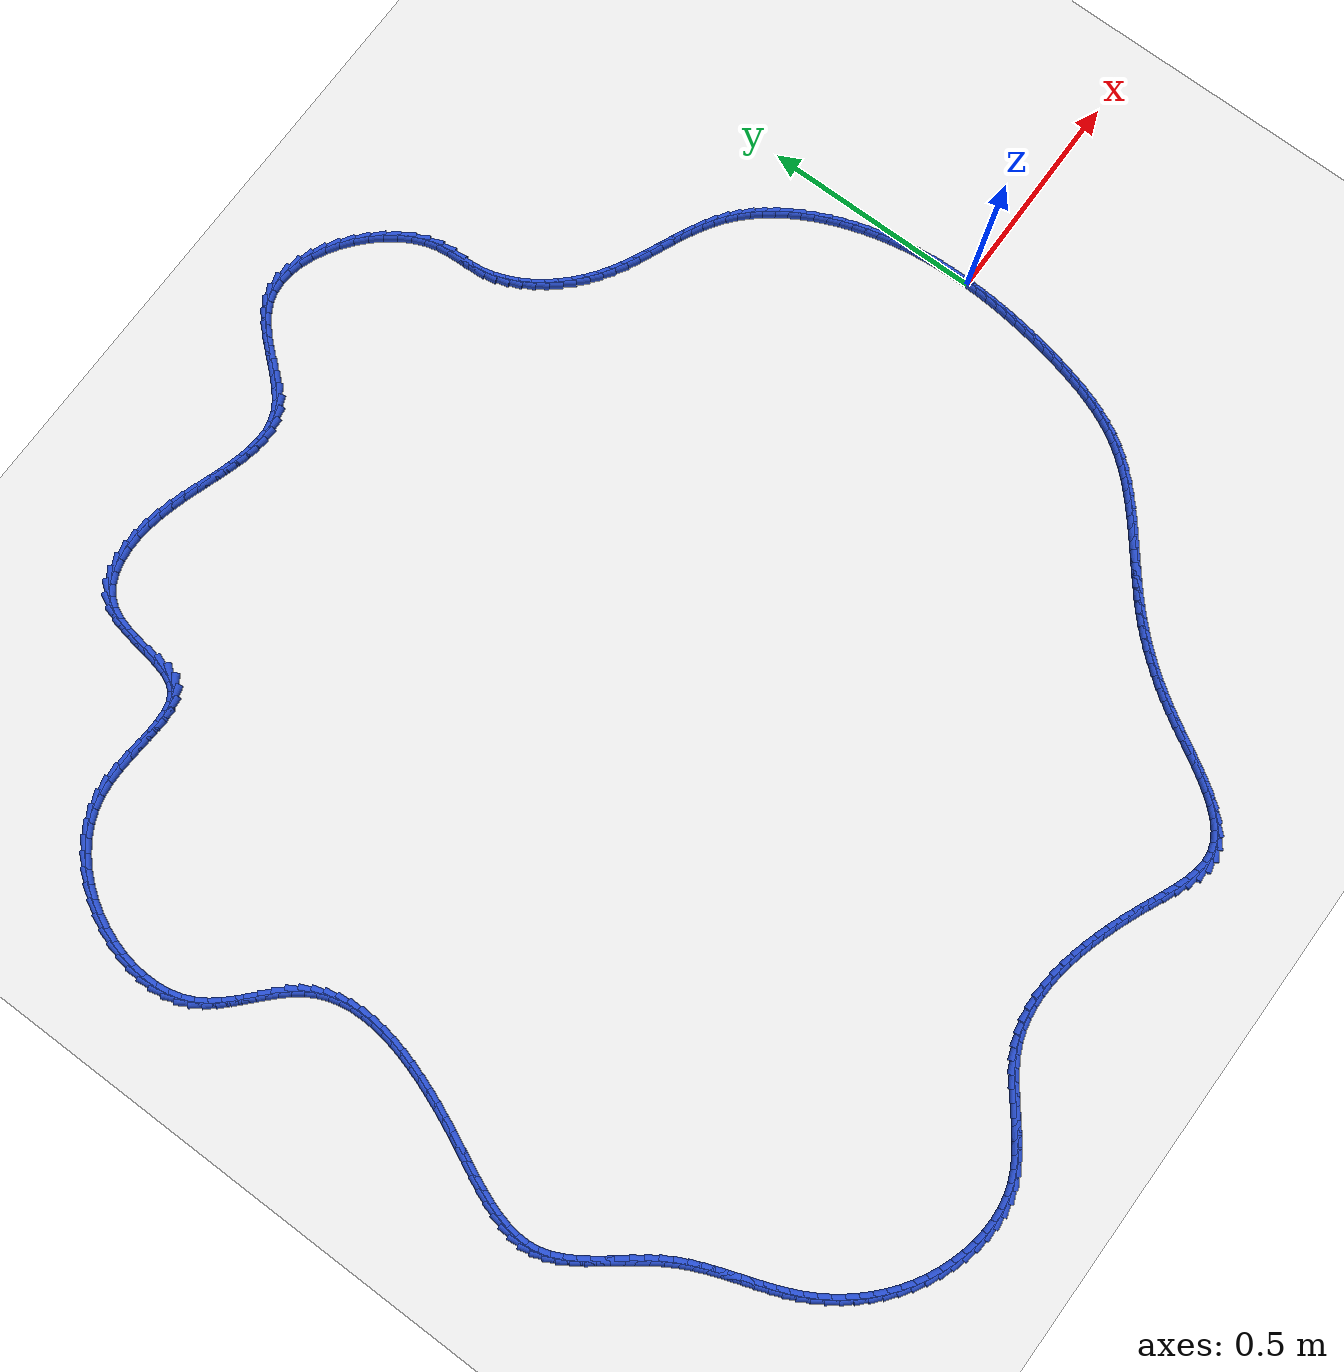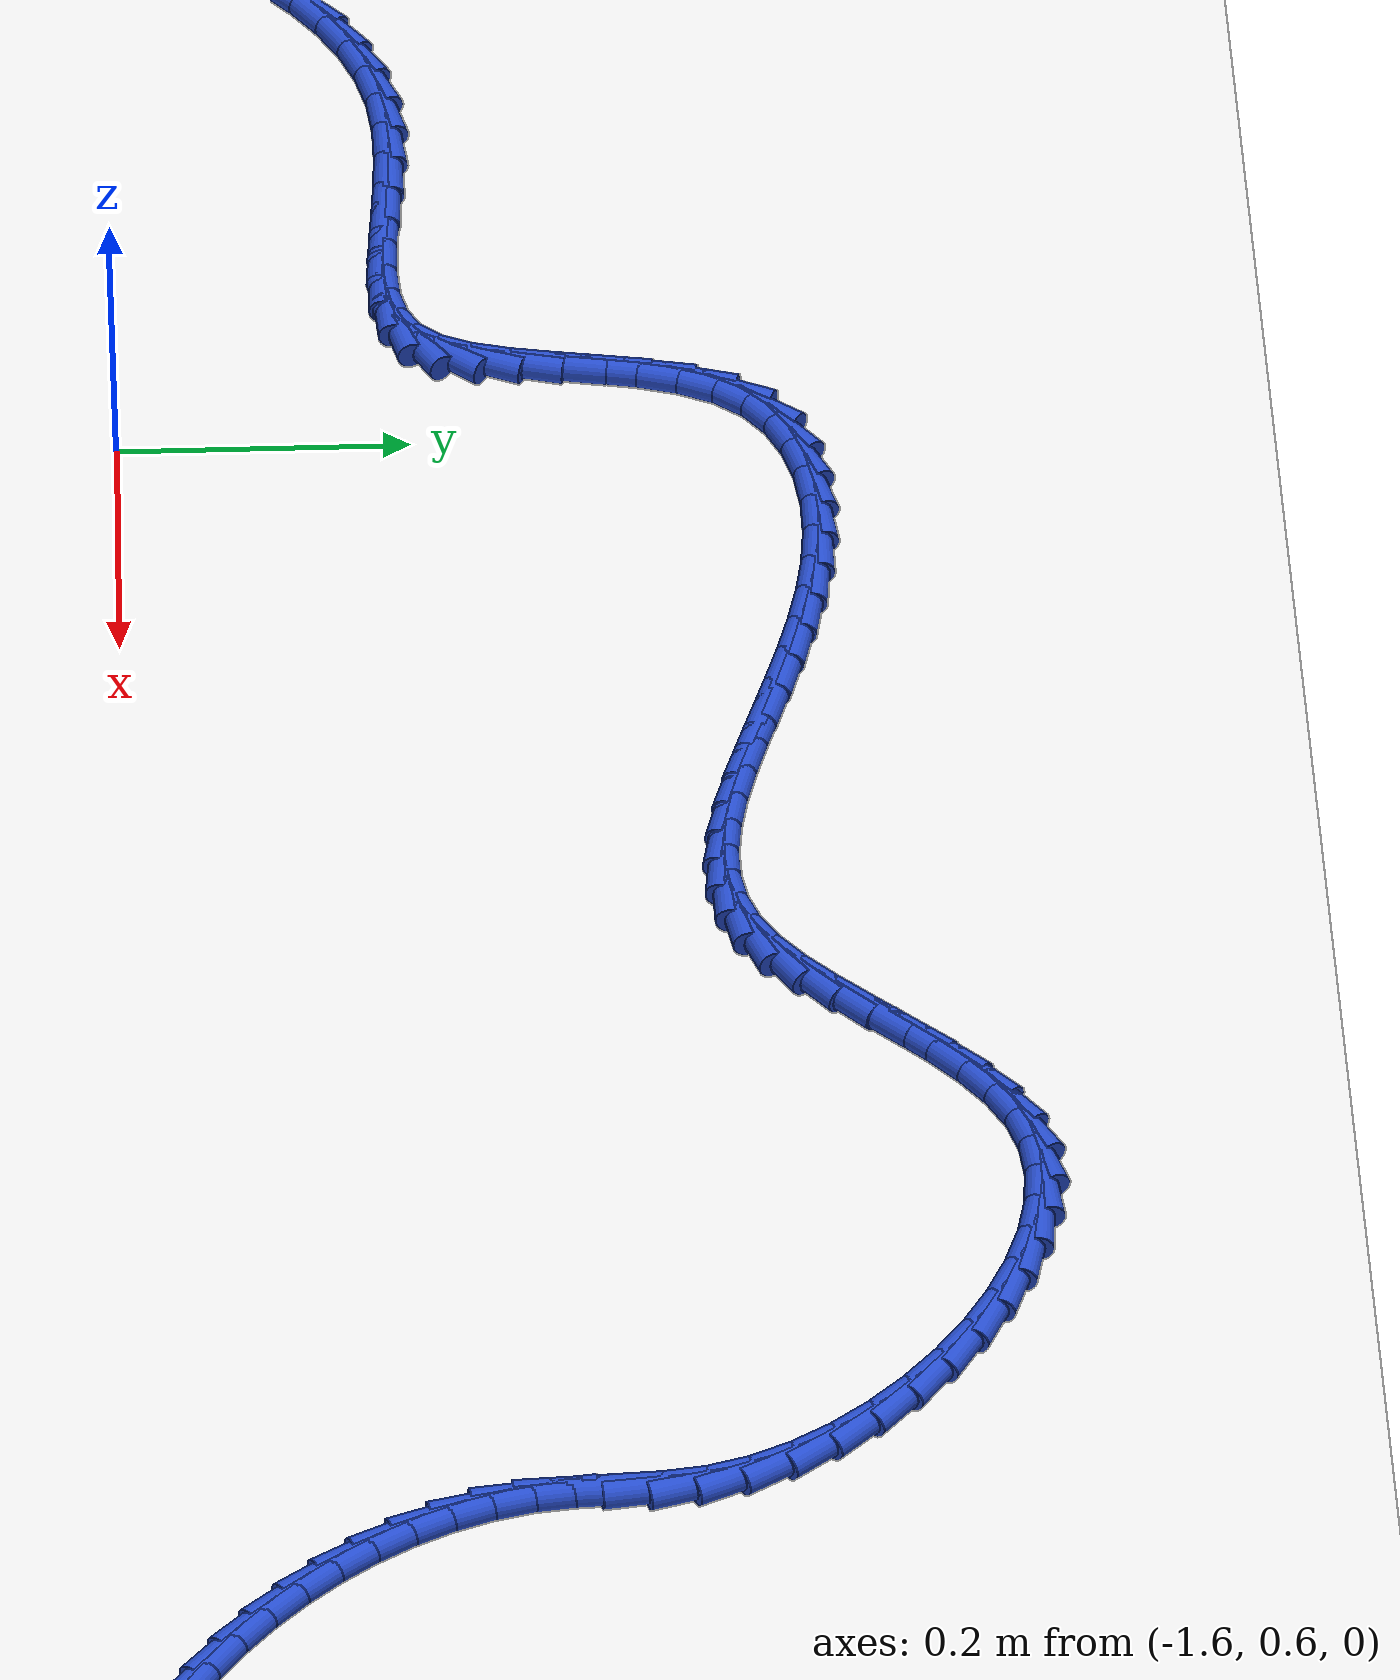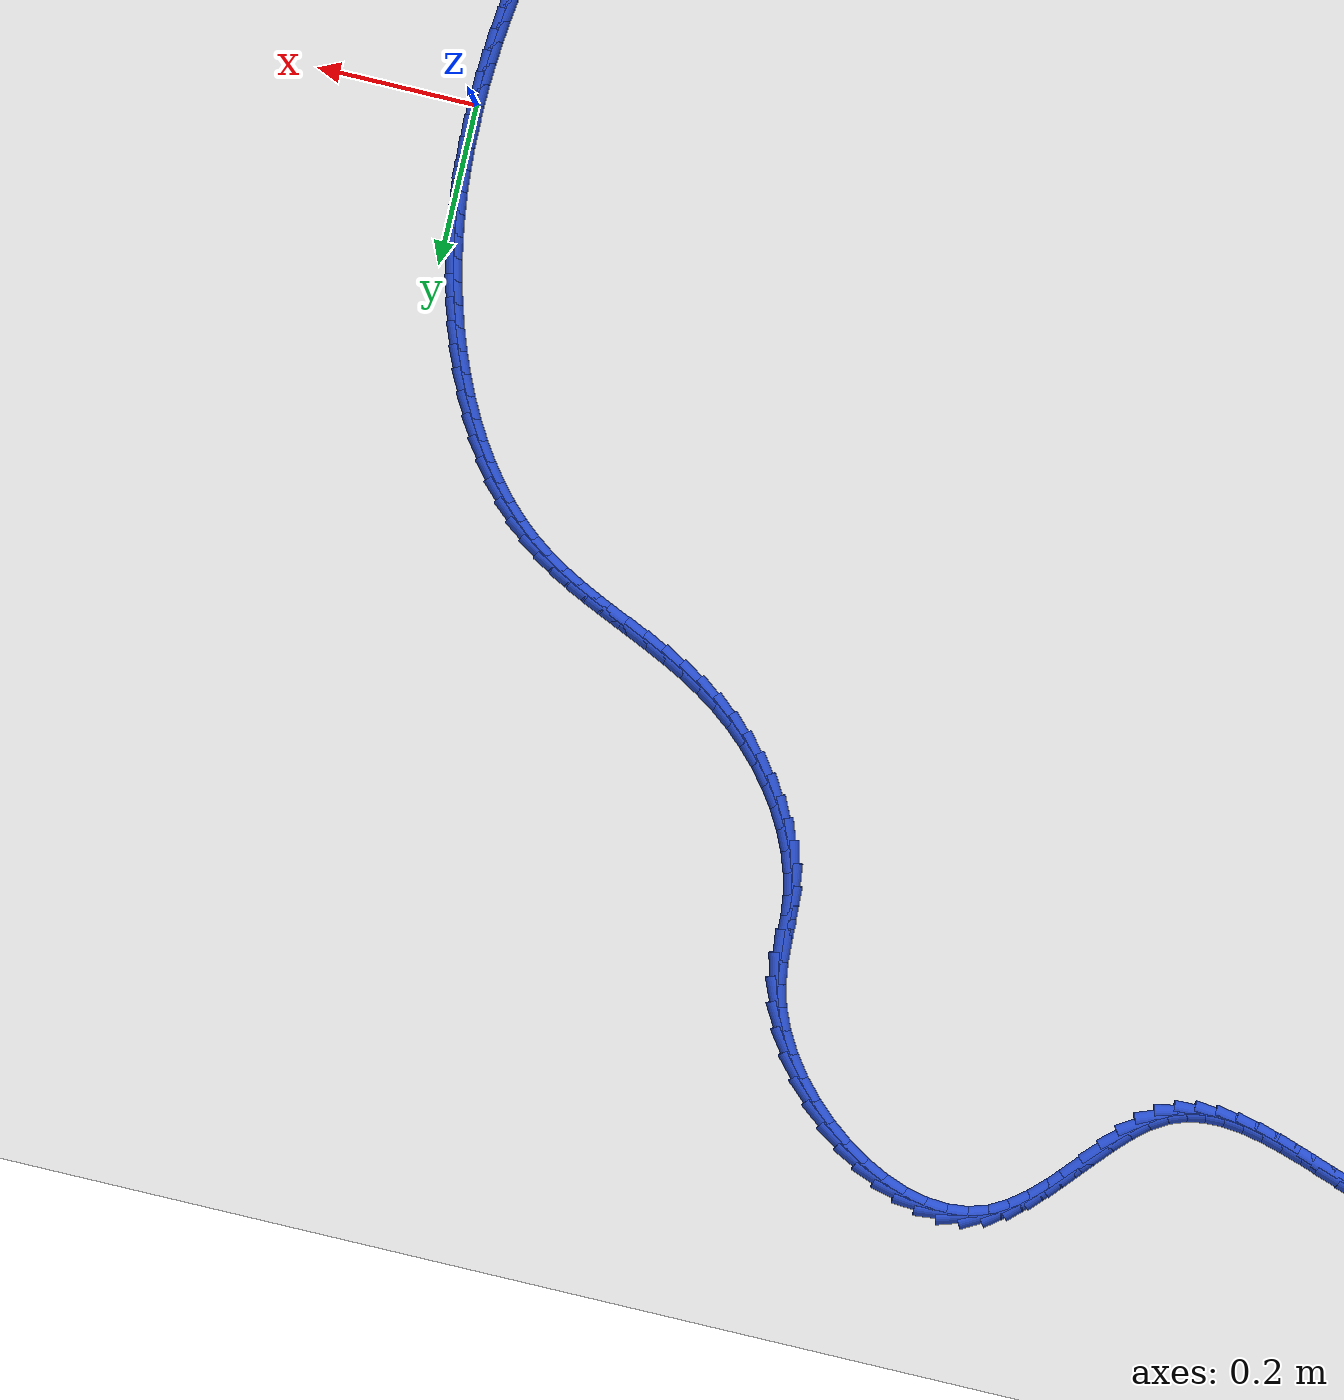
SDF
<sdf version="1.6">
 <world name="default">
  <light name="sun" type="directional">
   <pose>0 0 10 0 -0 0</pose>
   <diffuse>0.8 0.8 0.8 1</diffuse>
   <specular>0.2 0.2 0.2 1</specular>
   <attenuation>
    <range>1000</range>
    <constant>0.9</constant>
    <linear>0.01</linear>
    <quadratic>0.001</quadratic>
   </attenuation>
   <direction>-0.5 0.1 -0.9</direction>
  </light>
  <model name="ground_plane">
   <static>1</static>
   <link name="link">
    <collision name="collision">
     <geometry><plane><normal>0 0 1</normal><size>100 100</size></plane></geometry>
     <surface><friction><ode><mu>100</mu><mu2>50</mu2></ode></friction></surface>
    </collision>
    <visual name="visual">
     <cast_shadows>0</cast_shadows>
     <geometry><plane><normal>0 0 1</normal><size>100 100</size></plane></geometry>
     <material>
      <script><uri>file://media/materials/scripts/gazebo.material</uri><name>Gazebo/WhiteGlow</name></script>
     </material>
    </visual>
   </link>
  </model>
  <gravity>0 0 -9.8</gravity>
  <magnetic_field>6e-06 2.3e-05 -4.2e-05</magnetic_field>
  <atmosphere type="adiabatic"/>
  <physics name="default_physics" default="0" type="ode">
   <max_step_size>0.001</max_step_size>
   <real_time_factor>1</real_time_factor>
   <real_time_update_rate>1000</real_time_update_rate>
  </physics>
  <scene><ambient>0.4 0.4 0.4 1</ambient><background>0.7 0.7 0.7 1</background><shadows>1</shadows></scene>
  <spherical_coordinates>
   <surface_model>EARTH_WGS84</surface_model>
   <latitude_deg>0</latitude_deg>
   <longitude_deg>0</longitude_deg>
   <elevation>0</elevation>
   <heading_deg>0</heading_deg>
  </spherical_coordinates>
  <model name="line">
   <link name="link_0">
    <pose>3.469446951953614e-18 4.163336342344337e-17 0.01 0 1.57 1.5686046677415935</pose>
    <collision name="collision">
     <geometry><cylinder><radius>0.01</radius><length>0.08</length></cylinder></geometry>
    </collision>
    <visual name="visual">
     <material>
      <script><name>Gazebo/Blue</name><uri>file://media/materials/scripts/gazebo.material</uri></script>
     </material>
     <geometry><cylinder><radius>0.01</radius><length>0.08</length></cylinder></geometry>
    </visual>
   </link>
   <link name="link_1">
    <pose>5.986512938867445e-05 0.027314939085516483 0.01 0 1.57 -1.5446424900478535</pose>
    <collision name="collision">
     <geometry><cylinder><radius>0.01</radius><length>0.08</length></cylinder></geometry>
    </collision>
    <visual name="visual">
     <material>
      <script><name>Gazebo/Blue</name><uri>file://media/materials/scripts/gazebo.material</uri></script>
     </material>
     <geometry><cylinder><radius>0.01</radius><length>0.08</length></cylinder></geometry>
    </visual>
   </link>
   <link name="link_2">
    <pose>-0.0006548803368331179 0.054637220638812566 0.01 0 1.57 -1.514660698182164</pose>
    <collision name="collision">
     <geometry><cylinder><radius>0.01</radius><length>0.08</length></cylinder></geometry>
    </collision>
    <visual name="visual">
     <material>
      <script><name>Gazebo/Blue</name><uri>file://media/materials/scripts/gazebo.material</uri></script>
     </material>
     <geometry><cylinder><radius>0.01</radius><length>0.08</length></cylinder></geometry>
    </visual>
   </link>
   <link name="link_3">
    <pose>-0.0021904547829877177 0.08196320189536513 0.01 0 1.57 -1.4830975884616007</pose>
    <collision name="collision">
     <geometry><cylinder><radius>0.01</radius><length>0.08</length></cylinder></geometry>
    </collision>
    <visual name="visual">
     <material>
      <script><name>Gazebo/Blue</name><uri>file://media/materials/scripts/gazebo.material</uri></script>
     </material>
     <geometry><cylinder><radius>0.01</radius><length>0.08</length></cylinder></geometry>
    </visual>
   </link>
   <link name="link_4">
    <pose>-0.004593076593397466 0.10928924009065091 0.01 0 1.57 -1.450025670227744</pose>
    <collision name="collision">
     <geometry><cylinder><radius>0.01</radius><length>0.08</length></cylinder></geometry>
    </collision>
    <visual name="visual">
     <material>
      <script><name>Gazebo/Blue</name><uri>file://media/materials/scripts/gazebo.material</uri></script>
     </material>
     <geometry><cylinder><radius>0.01</radius><length>0.08</length></cylinder></geometry>
    </visual>
   </link>
   <link name="link_5">
    <pose>-0.007908964152384703 0.13661169246014668 0.01 0 1.57 -1.415536285359285</pose>
    <collision name="collision">
     <geometry><cylinder><radius>0.01</radius><length>0.08</length></cylinder></geometry>
    </collision>
    <visual name="visual">
     <material>
      <script><name>Gazebo/Blue</name><uri>file://media/materials/scripts/gazebo.material</uri></script>
     </material>
     <geometry><cylinder><radius>0.01</radius><length>0.08</length></cylinder></geometry>
    </visual>
   </link>
   <link name="link_6">
    <pose>-0.01218433584427178 0.16392691623932928 0.01 0 1.57 -1.379740339259799</pose>
    <collision name="collision">
     <geometry><cylinder><radius>0.01</radius><length>0.08</length></cylinder></geometry>
    </collision>
    <visual name="visual">
     <material>
      <script><name>Gazebo/Blue</name><uri>file://media/materials/scripts/gazebo.material</uri></script>
     </material>
     <geometry><cylinder><radius>0.01</radius><length>0.08</length></cylinder></geometry>
    </visual>
   </link>
   <link name="link_7">
    <pose>-0.017465410053381033 0.19123126866367549 0.01 0 1.57 -1.3427683134171196</pose>
    <collision name="collision">
     <geometry><cylinder><radius>0.01</radius><length>0.08</length></cylinder></geometry>
    </collision>
    <visual name="visual">
     <material>
      <script><name>Gazebo/Blue</name><uri>file://media/materials/scripts/gazebo.material</uri></script>
     </material>
     <geometry><cylinder><radius>0.01</radius><length>0.08</length></cylinder></geometry>
    </visual>
   </link>
   <link name="link_8">
    <pose>-0.023798405164034805 0.2185211069686621 0.01 0 1.57 -1.3047601957291866</pose>
    <collision name="collision">
     <geometry><cylinder><radius>0.01</radius><length>0.08</length></cylinder></geometry>
    </collision>
    <visual name="visual">
     <material>
      <script><name>Gazebo/Blue</name><uri>file://media/materials/scripts/gazebo.material</uri></script>
     </material>
     <geometry><cylinder><radius>0.01</radius><length>0.08</length></cylinder></geometry>
    </visual>
   </link>
   <link name="link_9">
    <pose>-0.031228597640717174 0.2457883378201303 0.01 0 1.57 -1.265589241247829</pose>
    <collision name="collision">
     <geometry><cylinder><radius>0.01</radius><length>0.08</length></cylinder></geometry>
    </collision>
    <visual name="visual">
     <material>
      <script><name>Gazebo/Blue</name><uri>file://media/materials/scripts/gazebo.material</uri></script>
     </material>
     <geometry><cylinder><radius>0.01</radius><length>0.08</length></cylinder></geometry>
    </visual>
   </link>
   <link name="link_10">
    <pose>-0.03978442922745219 0.27294532385834974 0.01 0 1.57 -1.2247531063989583</pose>
    <collision name="collision">
     <geometry><cylinder><radius>0.01</radius><length>0.08</length></cylinder></geometry>
    </collision>
    <visual name="visual">
     <material>
      <script><name>Gazebo/Blue</name><uri>file://media/materials/scripts/gazebo.material</uri></script>
     </material>
     <geometry><cylinder><radius>0.01</radius><length>0.08</length></cylinder></geometry>
    </visual>
   </link>
   <link name="link_11">
    <pose>-0.04947981975347978 0.2998358117009073 0.01 0 1.57 -1.181778552265423</pose>
    <collision name="collision">
     <geometry><cylinder><radius>0.01</radius><length>0.08</length></cylinder></geometry>
    </collision>
    <visual name="visual">
     <material>
      <script><name>Gazebo/Blue</name><uri>file://media/materials/scripts/gazebo.material</uri></script>
     </material>
     <geometry><cylinder><radius>0.01</radius><length>0.08</length></cylinder></geometry>
    </visual>
   </link>
   <link name="link_12">
    <pose>-0.06032821285854429 0.32630129797083257 0.01 0 1.57 -1.1361831632507438</pose>
    <collision name="collision">
     <geometry><cylinder><radius>0.01</radius><length>0.08</length></cylinder></geometry>
    </collision>
    <visual name="visual">
     <material>
      <script><name>Gazebo/Blue</name><uri>file://media/materials/scripts/gazebo.material</uri></script>
     </material>
     <geometry><cylinder><radius>0.01</radius><length>0.08</length></cylinder></geometry>
    </visual>
   </link>
   <link name="link_13">
    <pose>-0.07234305218239007 0.3521832792911548 0.01 0 1.57 -1.0874664741726738</pose>
    <collision name="collision">
     <geometry><cylinder><radius>0.01</radius><length>0.08</length></cylinder></geometry>
    </collision>
    <visual name="visual">
     <material>
      <script><name>Gazebo/Blue</name><uri>file://media/materials/scripts/gazebo.material</uri></script>
     </material>
     <geometry><cylinder><radius>0.01</radius><length>0.08</length></cylinder></geometry>
    </visual>
   </link>
   <link name="link_14">
    <pose>-0.08553778136476153 0.37732325228490365 0.01 0 1.57 -1.0351106886600607</pose>
    <collision name="collision">
     <geometry><cylinder><radius>0.01</radius><length>0.08</length></cylinder></geometry>
    </collision>
    <visual name="visual">
     <material>
      <script><name>Gazebo/Blue</name><uri>file://media/materials/scripts/gazebo.material</uri></script>
     </material>
     <geometry><cylinder><radius>0.01</radius><length>0.08</length></cylinder></geometry>
    </visual>
   </link>
   <link name="link_15">
    <pose>-0.099925844045403 0.4015627135751087 0.01 0 1.57 -0.9785882208468163</pose>
    <collision name="collision">
     <geometry><cylinder><radius>0.01</radius><length>0.08</length></cylinder></geometry>
    </collision>
    <visual name="visual">
     <material>
      <script><name>Gazebo/Blue</name><uri>file://media/materials/scripts/gazebo.material</uri></script>
     </material>
     <geometry><cylinder><radius>0.01</radius><length>0.08</length></cylinder></geometry>
    </visual>
   </link>
   <link name="link_16">
    <pose>-0.11552068386405884 0.4247431597847993 0.01 0 1.57 -0.9173787683518054</pose>
    <collision name="collision">
     <geometry><cylinder><radius>0.01</radius><length>0.08</length></cylinder></geometry>
    </collision>
    <visual name="visual">
     <material>
      <script><name>Gazebo/Blue</name><uri>file://media/materials/scripts/gazebo.material</uri></script>
     </material>
     <geometry><cylinder><radius>0.01</radius><length>0.08</length></cylinder></geometry>
    </visual>
   </link>
   <link name="link_17">
    <pose>-0.13233574446047347 0.44670608753700514 0.01 0 1.57 -0.8509992362033767</pose>
    <collision name="collision">
     <geometry><cylinder><radius>0.01</radius><length>0.08</length></cylinder></geometry>
    </collision>
    <visual name="visual">
     <material>
      <script><name>Gazebo/Blue</name><uri>file://media/materials/scripts/gazebo.material</uri></script>
     </material>
     <geometry><cylinder><radius>0.01</radius><length>0.08</length></cylinder></geometry>
    </visual>
   </link>
   <link name="link_18">
    <pose>-0.1503844694743911 0.46729299345475545 0.01 0 1.57 -0.7790497818089455</pose>
    <collision name="collision">
     <geometry><cylinder><radius>0.01</radius><length>0.08</length></cylinder></geometry>
    </collision>
    <visual name="visual">
     <material>
      <script><name>Gazebo/Blue</name><uri>file://media/materials/scripts/gazebo.material</uri></script>
     </material>
     <geometry><cylinder><radius>0.01</radius><length>0.08</length></cylinder></geometry>
    </visual>
   </link>
   <link name="link_19">
    <pose>-0.16968030254555638 0.48634537416108004 0.01 0 1.57 -0.7012777333331791</pose>
    <collision name="collision">
     <geometry><cylinder><radius>0.01</radius><length>0.08</length></cylinder></geometry>
    </collision>
    <visual name="visual">
     <material>
      <script><name>Gazebo/Blue</name><uri>file://media/materials/scripts/gazebo.material</uri></script>
     </material>
     <geometry><cylinder><radius>0.01</radius><length>0.08</length></cylinder></geometry>
    </visual>
   </link>
   <link name="link_20">
    <pose>-0.19023668731371335 0.5037047262790081 0.01 0 1.57 -0.6197250773368898</pose>
    <collision name="collision">
     <geometry><cylinder><radius>0.01</radius><length>0.08</length></cylinder></geometry>
    </collision>
    <visual name="visual">
     <material>
      <script><name>Gazebo/Blue</name><uri>file://media/materials/scripts/gazebo.material</uri></script>
     </material>
     <geometry><cylinder><radius>0.01</radius><length>0.08</length></cylinder></geometry>
    </visual>
   </link>
   <link name="link_21">
    <pose>-0.21204478315913225 0.5192646728340665 0.01 0 1.57 -0.5480218289737616</pose>
    <collision name="collision">
     <geometry><cylinder><radius>0.01</radius><length>0.08</length></cylinder></geometry>
    </collision>
    <visual name="visual">
     <material>
      <script><name>Gazebo/Blue</name><uri>file://media/materials/scripts/gazebo.material</uri></script>
     </material>
     <geometry><cylinder><radius>0.01</radius><length>0.08</length></cylinder></geometry>
    </visual>
   </link>
   <link name="link_22">
    <pose>-0.23495476489592204 0.5332486220192033 0.01 0 1.57 -0.49201042065135026</pose>
    <collision name="collision">
     <geometry><cylinder><radius>0.01</radius><length>0.08</length></cylinder></geometry>
    </collision>
    <visual name="visual">
     <material>
      <script><name>Gazebo/Blue</name><uri>file://media/materials/scripts/gazebo.material</uri></script>
     </material>
     <geometry><cylinder><radius>0.01</radius><length>0.08</length></cylinder></geometry>
    </visual>
   </link>
   <link name="link_23">
    <pose>-0.2587618331711567 0.5460085752867061 0.01 0 1.57 -0.45177811308489957</pose>
    <collision name="collision">
     <geometry><cylinder><radius>0.01</radius><length>0.08</length></cylinder></geometry>
    </collision>
    <visual name="visual">
     <material>
      <script><name>Gazebo/Blue</name><uri>file://media/materials/scripts/gazebo.material</uri></script>
     </material>
     <geometry><cylinder><radius>0.01</radius><length>0.08</length></cylinder></geometry>
    </visual>
   </link>
   <link name="link_24">
    <pose>-0.2832610637119321 0.5578968262964243 0.01 0 1.57 -0.42700411538172706</pose>
    <collision name="collision">
     <geometry><cylinder><radius>0.01</radius><length>0.08</length></cylinder></geometry>
    </collision>
    <visual name="visual">
     <material>
      <script><name>Gazebo/Blue</name><uri>file://media/materials/scripts/gazebo.material</uri></script>
     </material>
     <geometry><cylinder><radius>0.01</radius><length>0.08</length></cylinder></geometry>
    </visual>
   </link>
   <link name="link_25">
    <pose>-0.3082475322453435 0.5692656687082064 0.01 0 1.57 -0.41727077731692036</pose>
    <collision name="collision">
     <geometry><cylinder><radius>0.01</radius><length>0.08</length></cylinder></geometry>
    </collision>
    <visual name="visual">
     <material>
      <script><name>Gazebo/Blue</name><uri>file://media/materials/scripts/gazebo.material</uri></script>
     </material>
     <geometry><cylinder><radius>0.01</radius><length>0.08</length></cylinder></geometry>
    </visual>
   </link>
   <link name="link_26">
    <pose>-0.33351631449848634 0.5804673961819007 0.01 0 1.57 -0.42223459912199657</pose>
    <collision name="collision">
     <geometry><cylinder><radius>0.01</radius><length>0.08</length></cylinder></geometry>
    </collision>
    <visual name="visual">
     <material>
      <script><name>Gazebo/Blue</name><uri>file://media/materials/scripts/gazebo.material</uri></script>
     </material>
     <geometry><cylinder><radius>0.01</radius><length>0.08</length></cylinder></geometry>
    </visual>
   </link>
   <link name="link_27">
    <pose>-0.35886248619845623 0.5918543023773565 0.01 0 1.57 -0.4416844410322147</pose>
    <collision name="collision">
     <geometry><cylinder><radius>0.01</radius><length>0.08</length></cylinder></geometry>
    </collision>
    <visual name="visual">
     <material>
      <script><name>Gazebo/Blue</name><uri>file://media/materials/scripts/gazebo.material</uri></script>
     </material>
     <geometry><cylinder><radius>0.01</radius><length>0.08</length></cylinder></geometry>
    </visual>
   </link>
   <link name="link_28">
    <pose>-0.38408112307234854 0.6037786809544221 0.01 0 1.57 -0.4755044261012351</pose>
    <collision name="collision">
     <geometry><cylinder><radius>0.01</radius><length>0.08</length></cylinder></geometry>
    </collision>
    <visual name="visual">
     <material>
      <script><name>Gazebo/Blue</name><uri>file://media/materials/scripts/gazebo.material</uri></script>
     </material>
     <geometry><cylinder><radius>0.01</radius><length>0.08</length></cylinder></geometry>
    </visual>
   </link>
   <link name="link_29">
    <pose>-0.40896730084725863 0.6165928255729463 0.01 0 1.57 -0.5235501470863834</pose>
    <collision name="collision">
     <geometry><cylinder><radius>0.01</radius><length>0.08</length></cylinder></geometry>
    </collision>
    <visual name="visual">
     <material>
      <script><name>Gazebo/Blue</name><uri>file://media/materials/scripts/gazebo.material</uri></script>
     </material>
     <geometry><cylinder><radius>0.01</radius><length>0.08</length></cylinder></geometry>
    </visual>
   </link>
   <link name="link_30">
    <pose>-0.43331609525028225 0.6306490298927778 0.01 0 1.57 -0.5854405013461872</pose>
    <collision name="collision">
     <geometry><cylinder><radius>0.01</radius><length>0.08</length></cylinder></geometry>
    </collision>
    <visual name="visual">
     <material>
      <script><name>Gazebo/Blue</name><uri>file://media/materials/scripts/gazebo.material</uri></script>
     </material>
     <geometry><cylinder><radius>0.01</radius><length>0.08</length></cylinder></geometry>
    </visual>
   </link>
   <link name="link_31">
    <pose>-0.4569225730068366 0.6462994673175655 0.01 0 1.57 -0.6572251262831328</pose>
    <collision name="collision">
     <geometry><cylinder><radius>0.01</radius><length>0.08</length></cylinder></geometry>
    </collision>
    <visual name="visual">
     <material>
      <script><name>Gazebo/Blue</name><uri>file://media/materials/scripts/gazebo.material</uri></script>
     </material>
     <geometry><cylinder><radius>0.01</radius><length>0.08</length></cylinder></geometry>
    </visual>
   </link>
   <link name="link_32">
    <pose>-0.47957294778653214 0.6637780405391416 0.01 0 1.57 -0.7300106650848863</pose>
    <collision name="collision">
     <geometry><cylinder><radius>0.01</radius><length>0.08</length></cylinder></geometry>
    </collision>
    <visual name="visual">
     <material>
      <script><name>Gazebo/Blue</name><uri>file://media/materials/scripts/gazebo.material</uri></script>
     </material>
     <geometry><cylinder><radius>0.01</radius><length>0.08</length></cylinder></geometry>
    </visual>
   </link>
   <link name="link_33">
    <pose>-0.5010280058938634 0.6829789602111047 0.01 0 1.57 -0.8035669912949912</pose>
    <collision name="collision">
     <geometry><cylinder><radius>0.01</radius><length>0.08</length></cylinder></geometry>
    </collision>
    <visual name="visual">
     <material>
      <script><name>Gazebo/Blue</name><uri>file://media/materials/scripts/gazebo.material</uri></script>
     </material>
     <geometry><cylinder><radius>0.01</radius><length>0.08</length></cylinder></geometry>
    </visual>
   </link>
   <link name="link_34">
    <pose>-0.5210439967725442 0.7037358276601023 0.01 0 1.57 -0.8793226241603448</pose>
    <collision name="collision">
     <geometry><cylinder><radius>0.01</radius><length>0.08</length></cylinder></geometry>
    </collision>
    <visual name="visual">
     <material>
      <script><name>Gazebo/Blue</name><uri>file://media/materials/scripts/gazebo.material</uri></script>
     </material>
     <geometry><cylinder><radius>0.01</radius><length>0.08</length></cylinder></geometry>
    </visual>
   </link>
   <link name="link_35">
    <pose>-0.5393771698662879 0.7258822442127815 0.01 0 1.57 -0.958695840897123</pose>
    <collision name="collision">
     <geometry><cylinder><radius>0.01</radius><length>0.08</length></cylinder></geometry>
    </collision>
    <visual name="visual">
     <material>
      <script><name>Gazebo/Blue</name><uri>file://media/materials/scripts/gazebo.material</uri></script>
     </material>
     <geometry><cylinder><radius>0.01</radius><length>0.08</length></cylinder></geometry>
    </visual>
   </link>
   <link name="link_36">
    <pose>-0.5557837746188089 0.7492518111957895 0.01 0 1.57 -1.0431007285317389</pose>
    <collision name="collision">
     <geometry><cylinder><radius>0.01</radius><length>0.08</length></cylinder></geometry>
    </collision>
    <visual name="visual">
     <material>
      <script><name>Gazebo/Blue</name><uri>file://media/materials/scripts/gazebo.material</uri></script>
     </material>
     <geometry><cylinder><radius>0.01</radius><length>0.08</length></cylinder></geometry>
    </visual>
   </link>
   <link name="link_37">
    <pose>-0.5700200604738206 0.7736781299357737 0.01 0 1.57 -1.1339171846215697</pose>
    <collision name="collision">
     <geometry><cylinder><radius>0.01</radius><length>0.08</length></cylinder></geometry>
    </collision>
    <visual name="visual">
     <material>
      <script><name>Gazebo/Blue</name><uri>file://media/materials/scripts/gazebo.material</uri></script>
     </material>
     <geometry><cylinder><radius>0.01</radius><length>0.08</length></cylinder></geometry>
    </visual>
   </link>
   <link name="link_38">
    <pose>-0.5818422768750369 0.7989948017593809 0.01 0 1.57 -1.2324059413170694</pose>
    <collision name="collision">
     <geometry><cylinder><radius>0.01</radius><length>0.08</length></cylinder></geometry>
    </collision>
    <visual name="visual">
     <material>
      <script><name>Gazebo/Blue</name><uri>file://media/materials/scripts/gazebo.material</uri></script>
     </material>
     <geometry><cylinder><radius>0.01</radius><length>0.08</length></cylinder></geometry>
    </visual>
   </link>
   <link name="link_39">
    <pose>-0.5910066732661715 0.8250354279932587 0.01 0 1.57 -1.3395478475320086</pose>
    <collision name="collision">
     <geometry><cylinder><radius>0.01</radius><length>0.08</length></cylinder></geometry>
    </collision>
    <visual name="visual">
     <material>
      <script><name>Gazebo/Blue</name><uri>file://media/materials/scripts/gazebo.material</uri></script>
     </material>
     <geometry><cylinder><radius>0.01</radius><length>0.08</length></cylinder></geometry>
    </visual>
   </link>
   <link name="link_40">
    <pose>-0.5972694990909383 0.8516336099640538 0.01 0 1.57 -1.4525654030089392</pose>
    <collision name="collision">
     <geometry><cylinder><radius>0.01</radius><length>0.08</length></cylinder></geometry>
    </collision>
    <visual name="visual">
     <material>
      <script><name>Gazebo/Blue</name><uri>file://media/materials/scripts/gazebo.material</uri></script>
     </material>
     <geometry><cylinder><radius>0.01</radius><length>0.08</length></cylinder></geometry>
    </visual>
   </link>
   <link name="link_41">
    <pose>-0.6004758438016128 0.8786264697778471 0.01 0 1.57 -1.5244096772551385</pose>
    <collision name="collision">
     <geometry><cylinder><radius>0.01</radius><length>0.08</length></cylinder></geometry>
    </collision>
    <visual name="visual">
     <material>
      <script><name>Gazebo/Blue</name><uri>file://media/materials/scripts/gazebo.material</uri></script>
     </material>
     <geometry><cylinder><radius>0.01</radius><length>0.08</length></cylinder></geometry>
    </visual>
   </link>
   <link name="link_42">
    <pose>-0.6017419495823003 0.9059015060373831 0.01 0 1.57 -1.5201987381754465</pose>
    <collision name="collision">
     <geometry><cylinder><radius>0.01</radius><length>0.08</length></cylinder></geometry>
    </collision>
    <visual name="visual">
     <material>
      <script><name>Gazebo/Blue</name><uri>file://media/materials/scripts/gazebo.material</uri></script>
     </material>
     <geometry><cylinder><radius>0.01</radius><length>0.08</length></cylinder></geometry>
    </visual>
   </link>
   <link name="link_43">
    <pose>-0.6031336778463012 0.9333838512887804 0.01 0 1.57 -1.4409520958502824</pose>
    <collision name="collision">
     <geometry><cylinder><radius>0.01</radius><length>0.08</length></cylinder></geometry>
    </collision>
    <visual name="visual">
     <material>
      <script><name>Gazebo/Blue</name><uri>file://media/materials/scripts/gazebo.material</uri></script>
     </material>
     <geometry><cylinder><radius>0.01</radius><length>0.08</length></cylinder></geometry>
    </visual>
   </link>
   <link name="link_44">
    <pose>-0.606739704106439 0.9609995422137358 0.01 0 1.57 -1.3008586184596633</pose>
    <collision name="collision">
     <geometry><cylinder><radius>0.01</radius><length>0.08</length></cylinder></geometry>
    </collision>
    <visual name="visual">
     <material>
      <script><name>Gazebo/Blue</name><uri>file://media/materials/scripts/gazebo.material</uri></script>
     </material>
     <geometry><cylinder><radius>0.01</radius><length>0.08</length></cylinder></geometry>
    </visual>
   </link>
   <link name="link_45">
    <pose>-0.6143878155346838 0.9886408799483685 0.01 0 1.57 -1.1615517633464194</pose>
    <collision name="collision">
     <geometry><cylinder><radius>0.01</radius><length>0.08</length></cylinder></geometry>
    </collision>
    <visual name="visual">
     <material>
      <script><name>Gazebo/Blue</name><uri>file://media/materials/scripts/gazebo.material</uri></script>
     </material>
     <geometry><cylinder><radius>0.01</radius><length>0.08</length></cylinder></geometry>
    </visual>
   </link>
   <link name="link_46">
    <pose>-0.6262482303238928 1.0159858249125362 0.01 0 1.57 -1.0412513603657656</pose>
    <collision name="collision">
     <geometry><cylinder><radius>0.01</radius><length>0.08</length></cylinder></geometry>
    </collision>
    <visual name="visual">
     <material>
      <script><name>Gazebo/Blue</name><uri>file://media/materials/scripts/gazebo.material</uri></script>
     </material>
     <geometry><cylinder><radius>0.01</radius><length>0.08</length></cylinder></geometry>
    </visual>
   </link>
   <link name="link_47">
    <pose>-0.6418423069870076 1.0426284332962898 0.01 0 1.57 -0.9349334244067018</pose>
    <collision name="collision">
     <geometry><cylinder><radius>0.01</radius><length>0.08</length></cylinder></geometry>
    </collision>
    <visual name="visual">
     <material>
      <script><name>Gazebo/Blue</name><uri>file://media/materials/scripts/gazebo.material</uri></script>
     </material>
     <geometry><cylinder><radius>0.01</radius><length>0.08</length></cylinder></geometry>
    </visual>
   </link>
   <link name="link_48">
    <pose>-0.660689894379997 1.0681625660755074 0.01 0 1.57 -0.837903470407882</pose>
    <collision name="collision">
     <geometry><cylinder><radius>0.01</radius><length>0.08</length></cylinder></geometry>
    </collision>
    <visual name="visual">
     <material>
      <script><name>Gazebo/Blue</name><uri>file://media/materials/scripts/gazebo.material</uri></script>
     </material>
     <geometry><cylinder><radius>0.01</radius><length>0.08</length></cylinder></geometry>
    </visual>
   </link>
   <link name="link_49">
    <pose>-0.6823108413588309 1.0921820842260668 0.01 0 1.57 -0.7459646770855777</pose>
    <collision name="collision">
     <geometry><cylinder><radius>0.01</radius><length>0.08</length></cylinder></geometry>
    </collision>
    <visual name="visual">
     <material>
      <script><name>Gazebo/Blue</name><uri>file://media/materials/scripts/gazebo.material</uri></script>
     </material>
     <geometry><cylinder><radius>0.01</radius><length>0.08</length></cylinder></geometry>
    </visual>
   </link>
   <link name="link_50">
    <pose>-0.7062249967794783 1.114280848723846 0.01 0 1.57 -0.6552487908555923</pose>
    <collision name="collision">
     <geometry><cylinder><radius>0.01</radius><length>0.08</length></cylinder></geometry>
    </collision>
    <visual name="visual">
     <material>
      <script><name>Gazebo/Blue</name><uri>file://media/materials/scripts/gazebo.material</uri></script>
     </material>
     <geometry><cylinder><radius>0.01</radius><length>0.08</length></cylinder></geometry>
    </visual>
   </link>
   <link name="link_51">
    <pose>-0.7319522094979085 1.134052720544723 0.01 0 1.57 -0.5619476946103579</pose>
    <collision name="collision">
     <geometry><cylinder><radius>0.01</radius><length>0.08</length></cylinder></geometry>
    </collision>
    <visual name="visual">
     <material>
      <script><name>Gazebo/Blue</name><uri>file://media/materials/scripts/gazebo.material</uri></script>
     </material>
     <geometry><cylinder><radius>0.01</radius><length>0.08</length></cylinder></geometry>
    </visual>
   </link>
   <link name="link_52">
    <pose>-0.7590123283700912 1.151091560664576 0.01 0 1.57 -0.4620192932907896</pose>
    <collision name="collision">
     <geometry><cylinder><radius>0.01</radius><length>0.08</length></cylinder></geometry>
    </collision>
    <visual name="visual">
     <material>
      <script><name>Gazebo/Blue</name><uri>file://media/materials/scripts/gazebo.material</uri></script>
     </material>
     <geometry><cylinder><radius>0.01</radius><length>0.08</length></cylinder></geometry>
    </visual>
   </link>
   <link name="link_53">
    <pose>-0.7869252022519962 1.1649912300592837 0.01 0 1.57 -0.3509154581336053</pose>
    <collision name="collision">
     <geometry><cylinder><radius>0.01</radius><length>0.08</length></cylinder></geometry>
    </collision>
    <visual name="visual">
     <material>
      <script><name>Gazebo/Blue</name><uri>file://media/materials/scripts/gazebo.material</uri></script>
     </material>
     <geometry><cylinder><radius>0.01</radius><length>0.08</length></cylinder></geometry>
    </visual>
   </link>
   <link name="link_54">
    <pose>-0.8152106799995921 1.1753455897047231 0.01 0 1.57 -0.22343731287423077</pose>
    <collision name="collision">
     <geometry><cylinder><radius>0.01</radius><length>0.08</length></cylinder></geometry>
    </collision>
    <visual name="visual">
     <material>
      <script><name>Gazebo/Blue</name><uri>file://media/materials/scripts/gazebo.material</uri></script>
     </material>
     <geometry><cylinder><radius>0.01</radius><length>0.08</length></cylinder></geometry>
    </visual>
   </link>
   <link name="link_55">
    <pose>-0.8433886104688484 1.1817485005767718 0.01 0 1.57 -0.0739967911485349</pose>
    <collision name="collision">
     <geometry><cylinder><radius>0.01</radius><length>0.08</length></cylinder></geometry>
    </collision>
    <visual name="visual">
     <material>
      <script><name>Gazebo/Blue</name><uri>file://media/materials/scripts/gazebo.material</uri></script>
     </material>
     <geometry><cylinder><radius>0.01</radius><length>0.08</length></cylinder></geometry>
    </visual>
   </link>
   <link name="link_56">
    <pose>-0.8709788425157348 1.183793823651309 0.01 0 1.57 0.10213804169180339</pose>
    <collision name="collision">
     <geometry><cylinder><radius>0.01</radius><length>0.08</length></cylinder></geometry>
    </collision>
    <visual name="visual">
     <material>
      <script><name>Gazebo/Blue</name><uri>file://media/materials/scripts/gazebo.material</uri></script>
     </material>
     <geometry><cylinder><radius>0.01</radius><length>0.08</length></cylinder></geometry>
    </visual>
   </link>
   <link name="link_57">
    <pose>-0.8975012249962204 1.1810754199042124 0.01 0 1.57 0.3057237870185091</pose>
    <collision name="collision">
     <geometry><cylinder><radius>0.01</radius><length>0.08</length></cylinder></geometry>
    </collision>
    <visual name="visual">
     <material>
      <script><name>Gazebo/Blue</name><uri>file://media/materials/scripts/gazebo.material</uri></script>
     </material>
     <geometry><cylinder><radius>0.01</radius><length>0.08</length></cylinder></geometry>
    </visual>
   </link>
   <link name="link_58">
    <pose>-0.9224782676854394 1.1731921923618858 0.01 0 1.57 0.5084165595219025</pose>
    <collision name="collision">
     <geometry><cylinder><radius>0.01</radius><length>0.08</length></cylinder></geometry>
    </collision>
    <visual name="visual">
     <material>
      <script><name>Gazebo/Blue</name><uri>file://media/materials/scripts/gazebo.material</uri></script>
     </material>
     <geometry><cylinder><radius>0.01</radius><length>0.08</length></cylinder></geometry>
    </visual>
   </link>
   <link name="link_59">
    <pose>-0.9457004860533058 1.1602508754318395 0.01 0 1.57 0.6621634413331473</pose>
    <collision name="collision">
     <geometry><cylinder><radius>0.01</radius><length>0.08</length></cylinder></geometry>
    </collision>
    <visual name="visual">
     <material>
      <script><name>Gazebo/Blue</name><uri>file://media/materials/scripts/gazebo.material</uri></script>
     </material>
     <geometry><cylinder><radius>0.01</radius><length>0.08</length></cylinder></geometry>
    </visual>
   </link>
   <link name="link_60">
    <pose>-0.9674521410644032 1.1432937786282185 0.01 0 1.57 0.7659020343018577</pose>
    <collision name="collision">
     <geometry><cylinder><radius>0.01</radius><length>0.08</length></cylinder></geometry>
    </collision>
    <visual name="visual">
     <material>
      <script><name>Gazebo/Blue</name><uri>file://media/materials/scripts/gazebo.material</uri></script>
     </material>
     <geometry><cylinder><radius>0.01</radius><length>0.08</length></cylinder></geometry>
    </visual>
   </link>
   <link name="link_61">
    <pose>-0.9880706572309484 1.1234639485701832 0.01 0 1.57 0.8273411087327771</pose>
    <collision name="collision">
     <geometry><cylinder><radius>0.01</radius><length>0.08</length></cylinder></geometry>
    </collision>
    <visual name="visual">
     <material>
      <script><name>Gazebo/Blue</name><uri>file://media/materials/scripts/gazebo.material</uri></script>
     </material>
     <geometry><cylinder><radius>0.01</radius><length>0.08</length></cylinder></geometry>
    </visual>
   </link>
   <link name="link_62">
    <pose>-1.0078934590651611 1.1019044318768954 0.01 0 1.57 0.8523084880905474</pose>
    <collision name="collision">
     <geometry><cylinder><radius>0.01</radius><length>0.08</length></cylinder></geometry>
    </collision>
    <visual name="visual">
     <material>
      <script><name>Gazebo/Blue</name><uri>file://media/materials/scripts/gazebo.material</uri></script>
     </material>
     <geometry><cylinder><radius>0.01</radius><length>0.08</length></cylinder></geometry>
    </visual>
   </link>
   <link name="link_63">
    <pose>-1.0272579710792586 1.0797582751675154 0.01 0 1.57 0.8427905696882132</pose>
    <collision name="collision">
     <geometry><cylinder><radius>0.01</radius><length>0.08</length></cylinder></geometry>
    </collision>
    <visual name="visual">
     <material>
      <script><name>Gazebo/Blue</name><uri>file://media/materials/scripts/gazebo.material</uri></script>
     </material>
     <geometry><cylinder><radius>0.01</radius><length>0.08</length></cylinder></geometry>
    </visual>
   </link>
   <link name="link_64">
    <pose>-1.0465016177854598 1.0581685250612052 0.01 0 1.57 0.7963274735235107</pose>
    <collision name="collision">
     <geometry><cylinder><radius>0.01</radius><length>0.08</length></cylinder></geometry>
    </collision>
    <visual name="visual">
     <material>
      <script><name>Gazebo/Blue</name><uri>file://media/materials/scripts/gazebo.material</uri></script>
     </material>
     <geometry><cylinder><radius>0.01</radius><length>0.08</length></cylinder></geometry>
    </visual>
   </link>
   <link name="link_65">
    <pose>-1.065961823695982 1.0382782281771248 0.01 0 1.57 0.7055297412838324</pose>
    <collision name="collision">
     <geometry><cylinder><radius>0.01</radius><length>0.08</length></cylinder></geometry>
    </collision>
    <visual name="visual">
     <material>
      <script><name>Gazebo/Blue</name><uri>file://media/materials/scripts/gazebo.material</uri></script>
     </material>
     <geometry><cylinder><radius>0.01</radius><length>0.08</length></cylinder></geometry>
    </visual>
   </link>
   <link name="link_66">
    <pose>-1.085976013323044 1.0212304311344356 0.01 0 1.57 0.5585465601877885</pose>
    <collision name="collision">
     <geometry><cylinder><radius>0.01</radius><length>0.08</length></cylinder></geometry>
    </collision>
    <visual name="visual">
     <material>
      <script><name>Gazebo/Blue</name><uri>file://media/materials/scripts/gazebo.material</uri></script>
     </material>
     <geometry><cylinder><radius>0.01</radius><length>0.08</length></cylinder></geometry>
    </visual>
   </link>
   <link name="link_67">
    <pose>-1.1068811516995045 1.0081662532546927 0.01 0 1.57 0.36481598754508787</pose>
    <collision name="collision">
     <geometry><cylinder><radius>0.01</radius><length>0.08</length></cylinder></geometry>
    </collision>
    <visual name="visual">
     <material>
      <script><name>Gazebo/Blue</name><uri>file://media/materials/scripts/gazebo.material</uri></script>
     </material>
     <geometry><cylinder><radius>0.01</radius><length>0.08</length></cylinder></geometry>
    </visual>
   </link>
   <link name="link_68">
    <pose>-1.128902015918738 0.9997562387554104 0.01 0 1.57 0.1784628266542008</pose>
    <collision name="collision">
     <geometry><cylinder><radius>0.01</radius><length>0.08</length></cylinder></geometry>
    </collision>
    <visual name="visual">
     <material>
      <script><name>Gazebo/Blue</name><uri>file://media/materials/scripts/gazebo.material</uri></script>
     </material>
     <geometry><cylinder><radius>0.01</radius><length>0.08</length></cylinder></geometry>
    </visual>
   </link>
   <link name="link_69">
    <pose>-1.1520053979540479 0.9955888068478382 0.01 0 1.57 0.02023123148100873</pose>
    <collision name="collision">
     <geometry><cylinder><radius>0.01</radius><length>0.08</length></cylinder></geometry>
    </collision>
    <visual name="visual">
     <material>
      <script><name>Gazebo/Blue</name><uri>file://media/materials/scripts/gazebo.material</uri></script>
     </material>
     <geometry><cylinder><radius>0.01</radius><length>0.08</length></cylinder></geometry>
    </visual>
   </link>
   <link name="link_70">
    <pose>-1.1761219607196456 0.9951008325057747 0.01 0 1.57 -0.1044988635622168</pose>
    <collision name="collision">
     <geometry><cylinder><radius>0.01</radius><length>0.08</length></cylinder></geometry>
    </collision>
    <visual name="visual">
     <material>
      <script><name>Gazebo/Blue</name><uri>file://media/materials/scripts/gazebo.material</uri></script>
     </material>
     <geometry><cylinder><radius>0.01</radius><length>0.08</length></cylinder></geometry>
    </visual>
   </link>
   <link name="link_71">
    <pose>-1.201182367129746 0.9977291907030209 0.01 0 1.57 -0.19719472050677767</pose>
    <collision name="collision">
     <geometry><cylinder><radius>0.01</radius><length>0.08</length></cylinder></geometry>
    </collision>
    <visual name="visual">
     <material>
      <script><name>Gazebo/Blue</name><uri>file://media/materials/scripts/gazebo.material</uri></script>
     </material>
     <geometry><cylinder><radius>0.01</radius><length>0.08</length></cylinder></geometry>
    </visual>
   </link>
   <link name="link_72">
    <pose>-1.2271172800985612 1.0029107564133763 0.01 0 1.57 -0.2620319175073464</pose>
    <collision name="collision">
     <geometry><cylinder><radius>0.01</radius><length>0.08</length></cylinder></geometry>
    </collision>
    <visual name="visual">
     <material>
      <script><name>Gazebo/Blue</name><uri>file://media/materials/scripts/gazebo.material</uri></script>
     </material>
     <geometry><cylinder><radius>0.01</radius><length>0.08</length></cylinder></geometry>
    </visual>
   </link>
   <link name="link_73">
    <pose>-1.2538573625403044 1.0100824046106411 0.01 0 1.57 -0.30329538065270734</pose>
    <collision name="collision">
     <geometry><cylinder><radius>0.01</radius><length>0.08</length></cylinder></geometry>
    </collision>
    <visual name="visual">
     <material>
      <script><name>Gazebo/Blue</name><uri>file://media/materials/scripts/gazebo.material</uri></script>
     </material>
     <geometry><cylinder><radius>0.01</radius><length>0.08</length></cylinder></geometry>
    </visual>
   </link>
   <link name="link_74">
    <pose>-1.2813332773691888 1.0186810102686155 0.01 0 1.57 -0.32435897336050806</pose>
    <collision name="collision">
     <geometry><cylinder><radius>0.01</radius><length>0.08</length></cylinder></geometry>
    </collision>
    <visual name="visual">
     <material>
      <script><name>Gazebo/Blue</name><uri>file://media/materials/scripts/gazebo.material</uri></script>
     </material>
     <geometry><cylinder><radius>0.01</radius><length>0.08</length></cylinder></geometry>
    </visual>
   </link>
   <link name="link_75">
    <pose>-1.3094756874994273 1.0281434483610994 0.01 0 1.57 -0.3274793681051528</pose>
    <collision name="collision">
     <geometry><cylinder><radius>0.01</radius><length>0.08</length></cylinder></geometry>
    </collision>
    <visual name="visual">
     <material>
      <script><name>Gazebo/Blue</name><uri>file://media/materials/scripts/gazebo.material</uri></script>
     </material>
     <geometry><cylinder><radius>0.01</radius><length>0.08</length></cylinder></geometry>
    </visual>
   </link>
   <link name="link_76">
    <pose>-1.338215255845233 1.037906593861893 0.01 0 1.57 -0.31388655361402984</pose>
    <collision name="collision">
     <geometry><cylinder><radius>0.01</radius><length>0.08</length></cylinder></geometry>
    </collision>
    <visual name="visual">
     <material>
      <script><name>Gazebo/Blue</name><uri>file://media/materials/scripts/gazebo.material</uri></script>
     </material>
     <geometry><cylinder><radius>0.01</radius><length>0.08</length></cylinder></geometry>
    </visual>
   </link>
   <link name="link_77">
    <pose>-1.3674826453208189 1.047407321744796 0.01 0 1.57 -0.2839534213955684</pose>
    <collision name="collision">
     <geometry><cylinder><radius>0.01</radius><length>0.08</length></cylinder></geometry>
    </collision>
    <visual name="visual">
     <material>
      <script><name>Gazebo/Blue</name><uri>file://media/materials/scripts/gazebo.material</uri></script>
     </material>
     <geometry><cylinder><radius>0.01</radius><length>0.08</length></cylinder></geometry>
    </visual>
   </link>
   <link name="link_78">
    <pose>-1.397208518840398 1.056082506983609 0.01 0 1.57 -0.23739386927225803</pose>
    <collision name="collision">
     <geometry><cylinder><radius>0.01</radius><length>0.08</length></cylinder></geometry>
    </collision>
    <visual name="visual">
     <material>
      <script><name>Gazebo/Blue</name><uri>file://media/materials/scripts/gazebo.material</uri></script>
     </material>
     <geometry><cylinder><radius>0.01</radius><length>0.08</length></cylinder></geometry>
    </visual>
   </link>
   <link name="link_79">
    <pose>-1.4273235393181836 1.0633690245521317 0.01 0 1.57 -0.17352077001351604</pose>
    <collision name="collision">
     <geometry><cylinder><radius>0.01</radius><length>0.08</length></cylinder></geometry>
    </collision>
    <visual name="visual">
     <material>
      <script><name>Gazebo/Blue</name><uri>file://media/materials/scripts/gazebo.material</uri></script>
     </material>
     <geometry><cylinder><radius>0.01</radius><length>0.08</length></cylinder></geometry>
    </visual>
   </link>
   <link name="link_80">
    <pose>-1.4577583696683878 1.0687037494241642 0.01 0 1.57 -0.091637704188161</pose>
    <collision name="collision">
     <geometry><cylinder><radius>0.01</radius><length>0.08</length></cylinder></geometry>
    </collision>
    <visual name="visual">
     <material>
      <script><name>Gazebo/Blue</name><uri>file://media/materials/scripts/gazebo.material</uri></script>
     </material>
     <geometry><cylinder><radius>0.01</radius><length>0.08</length></cylinder></geometry>
    </visual>
   </link>
   <link name="link_81">
    <pose>-1.4884435978979764 1.0715235708347657 0.01 0 1.57 0.007188545871210958</pose>
    <collision name="collision">
     <geometry><cylinder><radius>0.01</radius><length>0.08</length></cylinder></geometry>
    </collision>
    <visual name="visual">
     <material>
      <script><name>Gazebo/Blue</name><uri>file://media/materials/scripts/gazebo.material</uri></script>
     </material>
     <geometry><cylinder><radius>0.01</radius><length>0.08</length></cylinder></geometry>
    </visual>
   </link>
   <link name="link_82">
    <pose>-1.5191116329108416 1.0713031084608042 0.01 0 1.57 0.12260518350929396</pose>
    <collision name="collision">
     <geometry><cylinder><radius>0.01</radius><length>0.08</length></cylinder></geometry>
    </collision>
    <visual name="visual">
     <material>
      <script><name>Gazebo/Blue</name><uri>file://media/materials/scripts/gazebo.material</uri></script>
     </material>
     <geometry><cylinder><radius>0.01</radius><length>0.08</length></cylinder></geometry>
    </visual>
   </link>
   <link name="link_83">
    <pose>-1.5488664950908604 1.0676366180866856 0.01 0 1.57 0.26313598196929044</pose>
    <collision name="collision">
     <geometry><cylinder><radius>0.01</radius><length>0.08</length></cylinder></geometry>
    </collision>
    <visual name="visual">
     <material>
      <script><name>Gazebo/Blue</name><uri>file://media/materials/scripts/gazebo.material</uri></script>
     </material>
     <geometry><cylinder><radius>0.01</radius><length>0.08</length></cylinder></geometry>
    </visual>
   </link>
   <link name="link_84">
    <pose>-1.5766879469352846 1.0601420124055823 0.01 0 1.57 0.4399187052784023</pose>
    <collision name="collision">
     <geometry><cylinder><radius>0.01</radius><length>0.08</length></cylinder></geometry>
    </collision>
    <visual name="visual">
     <material>
      <script><name>Gazebo/Blue</name><uri>file://media/materials/scripts/gazebo.material</uri></script>
     </material>
     <geometry><cylinder><radius>0.01</radius><length>0.08</length></cylinder></geometry>
    </visual>
   </link>
   <link name="link_85">
    <pose>-1.6015557509413654 1.048437204110666 0.01 0 1.57 0.6624215820329582</pose>
    <collision name="collision">
     <geometry><cylinder><radius>0.01</radius><length>0.08</length></cylinder></geometry>
    </collision>
    <visual name="visual">
     <material>
      <script><name>Gazebo/Blue</name><uri>file://media/materials/scripts/gazebo.material</uri></script>
     </material>
     <geometry><cylinder><radius>0.01</radius><length>0.08</length></cylinder></geometry>
    </visual>
   </link>
   <link name="link_86">
    <pose>-1.6224496696063537 1.032140105895108 0.01 0 1.57 0.9260604812209172</pose>
    <collision name="collision">
     <geometry><cylinder><radius>0.01</radius><length>0.08</length></cylinder></geometry>
    </collision>
    <visual name="visual">
     <material>
      <script><name>Gazebo/Blue</name><uri>file://media/materials/scripts/gazebo.material</uri></script>
     </material>
     <geometry><cylinder><radius>0.01</radius><length>0.08</length></cylinder></geometry>
    </visual>
   </link>
   <link name="link_87">
    <pose>-1.6384091102255478 1.0109154998745653 0.01 0 1.57 1.1574450267556815</pose>
    <collision name="collision">
     <geometry><cylinder><radius>0.01</radius><length>0.08</length></cylinder></geometry>
    </collision>
    <visual name="visual">
     <material>
      <script><name>Gazebo/Blue</name><uri>file://media/materials/scripts/gazebo.material</uri></script>
     </material>
     <geometry><cylinder><radius>0.01</radius><length>0.08</length></cylinder></geometry>
    </visual>
   </link>
   <link name="link_88">
    <pose>-1.6496288101996746 0.9853360370249079 0.01 0 1.57 1.3065759386264886</pose>
    <collision name="collision">
     <geometry><cylinder><radius>0.01</radius><length>0.08</length></cylinder></geometry>
    </collision>
    <visual name="visual">
     <material>
      <script><name>Gazebo/Blue</name><uri>file://media/materials/scripts/gazebo.material</uri></script>
     </material>
     <geometry><cylinder><radius>0.01</radius><length>0.08</length></cylinder></geometry>
    </visual>
   </link>
   <link name="link_89">
    <pose>-1.6573500015796574 0.9567967132958185 0.01 0 1.57 1.389860307310818</pose>
    <collision name="collision">
     <geometry><cylinder><radius>0.01</radius><length>0.08</length></cylinder></geometry>
    </collision>
    <visual name="visual">
     <material>
      <script><name>Gazebo/Blue</name><uri>file://media/materials/scripts/gazebo.material</uri></script>
     </material>
     <geometry><cylinder><radius>0.01</radius><length>0.08</length></cylinder></geometry>
    </visual>
   </link>
   <link name="link_90">
    <pose>-1.6628517273051968 0.9267222367758183 0.01 0 1.57 1.4208190525033726</pose>
    <collision name="collision">
     <geometry><cylinder><radius>0.01</radius><length>0.08</length></cylinder></geometry>
    </collision>
    <visual name="visual">
     <material>
      <script><name>Gazebo/Blue</name><uri>file://media/materials/scripts/gazebo.material</uri></script>
     </material>
     <geometry><cylinder><radius>0.01</radius><length>0.08</length></cylinder></geometry>
    </visual>
   </link>
   <link name="link_91">
    <pose>-1.667413030315993 0.8965373155534293 0.01 0 1.57 1.4026784795362457</pose>
    <collision name="collision">
     <geometry><cylinder><radius>0.01</radius><length>0.08</length></cylinder></geometry>
    </collision>
    <visual name="visual">
     <material>
      <script><name>Gazebo/Blue</name><uri>file://media/materials/scripts/gazebo.material</uri></script>
     </material>
     <geometry><cylinder><radius>0.01</radius><length>0.08</length></cylinder></geometry>
    </visual>
   </link>
   <link name="link_92">
    <pose>-1.6723129535517458 0.8676666577171721 0.01 0 1.57 1.3263700624506318</pose>
    <collision name="collision">
     <geometry><cylinder><radius>0.01</radius><length>0.08</length></cylinder></geometry>
    </collision>
    <visual name="visual">
     <material>
      <script><name>Gazebo/Blue</name><uri>file://media/materials/scripts/gazebo.material</uri></script>
     </material>
     <geometry><cylinder><radius>0.01</radius><length>0.08</length></cylinder></geometry>
    </visual>
   </link>
   <link name="link_93">
    <pose>-1.6788305399521553 0.8415349713555683 0.01 0 1.57 1.1659263671518523</pose>
    <collision name="collision">
     <geometry><cylinder><radius>0.01</radius><length>0.08</length></cylinder></geometry>
    </collision>
    <visual name="visual">
     <material>
      <script><name>Gazebo/Blue</name><uri>file://media/materials/scripts/gazebo.material</uri></script>
     </material>
     <geometry><cylinder><radius>0.01</radius><length>0.08</length></cylinder></geometry>
    </visual>
   </link>
   <link name="link_94">
    <pose>-1.6882448324569215 0.8195669645571394 0.01 0 1.57 0.8798644883373692</pose>
    <collision name="collision">
     <geometry><cylinder><radius>0.01</radius><length>0.08</length></cylinder></geometry>
    </collision>
    <visual name="visual">
     <material>
      <script><name>Gazebo/Blue</name><uri>file://media/materials/scripts/gazebo.material</uri></script>
     </material>
     <geometry><cylinder><radius>0.01</radius><length>0.08</length></cylinder></geometry>
    </visual>
   </link>
   <link name="link_95">
    <pose>-1.7018130168154253 0.8031585471232914 0.01 0 1.57 0.5252991789234338</pose>
    <collision name="collision">
     <geometry><cylinder><radius>0.01</radius><length>0.08</length></cylinder></geometry>
    </collision>
    <visual name="visual">
     <material>
      <script><name>Gazebo/Blue</name><uri>file://media/materials/scripts/gazebo.material</uri></script>
     </material>
     <geometry><cylinder><radius>0.01</radius><length>0.08</length></cylinder></geometry>
    </visual>
   </link>
   <link name="link_96">
    <pose>-1.71997641975837 0.7926306808898904 0.01 0 1.57 0.25166398617376795</pose>
    <collision name="collision">
     <geometry><cylinder><radius>0.01</radius><length>0.08</length></cylinder></geometry>
    </collision>
    <visual name="visual">
     <material>
      <script><name>Gazebo/Blue</name><uri>file://media/materials/scripts/gazebo.material</uri></script>
     </material>
     <geometry><cylinder><radius>0.01</radius><length>0.08</length></cylinder></geometry>
    </visual>
   </link>
   <link name="link_97">
    <pose>-1.7421357095736396 0.7869331916872968 0.01 0 1.57 0.07855775562547603</pose>
    <collision name="collision">
     <geometry><cylinder><radius>0.01</radius><length>0.08</length></cylinder></geometry>
    </collision>
    <visual name="visual">
     <material>
      <script><name>Gazebo/Blue</name><uri>file://media/materials/scripts/gazebo.material</uri></script>
     </material>
     <geometry><cylinder><radius>0.01</radius><length>0.08</length></cylinder></geometry>
    </visual>
   </link>
   <link name="link_98">
    <pose>-1.7676239010746335 0.7849267674395708 0.01 0 1.57 -0.019369745558864695</pose>
    <collision name="collision">
     <geometry><cylinder><radius>0.01</radius><length>0.08</length></cylinder></geometry>
    </collision>
    <visual name="visual">
     <material>
      <script><name>Gazebo/Blue</name><uri>file://media/materials/scripts/gazebo.material</uri></script>
     </material>
     <geometry><cylinder><radius>0.01</radius><length>0.08</length></cylinder></geometry>
    </visual>
   </link>
   <link name="link_99">
    <pose>-1.79577400907475 0.7854720960707724 0.01 0 1.57 -0.06485391614003358</pose>
    <collision name="collision">
     <geometry><cylinder><radius>0.01</radius><length>0.08</length></cylinder></geometry>
    </collision>
    <visual name="visual">
     <material>
      <script><name>Gazebo/Blue</name><uri>file://media/materials/scripts/gazebo.material</uri></script>
     </material>
     <geometry><cylinder><radius>0.01</radius><length>0.08</length></cylinder></geometry>
    </visual>
   </link>
   <link name="link_100">
    <pose>-1.8259190483873897 0.7874298655049625 0.01 0 1.57 -0.07076459542782498</pose>
    <collision name="collision">
     <geometry><cylinder><radius>0.01</radius><length>0.08</length></cylinder></geometry>
    </collision>
    <visual name="visual">
     <material>
      <script><name>Gazebo/Blue</name><uri>file://media/materials/scripts/gazebo.material</uri></script>
     </material>
     <geometry><cylinder><radius>0.01</radius><length>0.08</length></cylinder></geometry>
    </visual>
   </link>
   <link name="link_101">
    <pose>-1.8573920338259489 0.7896607636662007 0.01 0 1.57 -0.04244406172097629</pose>
    <collision name="collision">
     <geometry><cylinder><radius>0.01</radius><length>0.08</length></cylinder></geometry>
    </collision>
    <visual name="visual">
     <material>
      <script><name>Gazebo/Blue</name><uri>file://media/materials/scripts/gazebo.material</uri></script>
     </material>
     <geometry><cylinder><radius>0.01</radius><length>0.08</length></cylinder></geometry>
    </visual>
   </link>
   <link name="link_102">
    <pose>-1.8895259802038278 0.7910254784785478 0.01 0 1.57 0.01994202005533072</pose>
    <collision name="collision">
     <geometry><cylinder><radius>0.01</radius><length>0.08</length></cylinder></geometry>
    </collision>
    <visual name="visual">
     <material>
      <script><name>Gazebo/Blue</name><uri>file://media/materials/scripts/gazebo.material</uri></script>
     </material>
     <geometry><cylinder><radius>0.01</radius><length>0.08</length></cylinder></geometry>
    </visual>
   </link>
   <link name="link_103">
    <pose>-1.9216539023344252 0.7903846978660638 0.01 0 1.57 0.1197736101527017</pose>
    <collision name="collision">
     <geometry><cylinder><radius>0.01</radius><length>0.08</length></cylinder></geometry>
    </collision>
    <visual name="visual">
     <material>
      <script><name>Gazebo/Blue</name><uri>file://media/materials/scripts/gazebo.material</uri></script>
     </material>
     <geometry><cylinder><radius>0.01</radius><length>0.08</length></cylinder></geometry>
    </visual>
   </link>
   <link name="link_104">
    <pose>-1.9531088150311393 0.7865991097528088 0.01 0 1.57 0.2551713370753415</pose>
    <collision name="collision">
     <geometry><cylinder><radius>0.01</radius><length>0.08</length></cylinder></geometry>
    </collision>
    <visual name="visual">
     <material>
      <script><name>Gazebo/Blue</name><uri>file://media/materials/scripts/gazebo.material</uri></script>
     </material>
     <geometry><cylinder><radius>0.01</radius><length>0.08</length></cylinder></geometry>
    </visual>
   </link>
   <link name="link_105">
    <pose>-1.9832912446681092 0.7787257887820521 0.01 0 1.57 0.39341340836434896</pose>
    <collision name="collision">
     <geometry><cylinder><radius>0.01</radius><length>0.08</length></cylinder></geometry>
    </collision>
    <visual name="visual">
     <material>
      <script><name>Gazebo/Blue</name><uri>file://media/materials/scripts/gazebo.material</uri></script>
     </material>
     <geometry><cylinder><radius>0.01</radius><length>0.08</length></cylinder></geometry>
    </visual>
   </link>
   <link name="link_106">
    <pose>-2.0119488002804995 0.7668314503807531 0.01 0 1.57 0.5219724922034519</pose>
    <collision name="collision">
     <geometry><cylinder><radius>0.01</radius><length>0.08</length></cylinder></geometry>
    </collision>
    <visual name="visual">
     <material>
      <script><name>Gazebo/Blue</name><uri>file://media/materials/scripts/gazebo.material</uri></script>
     </material>
     <geometry><cylinder><radius>0.01</radius><length>0.08</length></cylinder></geometry>
    </visual>
   </link>
   <link name="link_107">
    <pose>-2.038940318282932 0.7513063631554833 0.01 0 1.57 0.6403717103904953</pose>
    <collision name="collision">
     <geometry><cylinder><radius>0.01</radius><length>0.08</length></cylinder></geometry>
    </collision>
    <visual name="visual">
     <material>
      <script><name>Gazebo/Blue</name><uri>file://media/materials/scripts/gazebo.material</uri></script>
     </material>
     <geometry><cylinder><radius>0.01</radius><length>0.08</length></cylinder></geometry>
    </visual>
   </link>
   <link name="link_108">
    <pose>-2.0641246857917497 0.7325409432008005 0.01 0 1.57 0.7492775264098542</pose>
    <collision name="collision">
     <geometry><cylinder><radius>0.01</radius><length>0.08</length></cylinder></geometry>
    </collision>
    <visual name="visual">
     <material>
      <script><name>Gazebo/Blue</name><uri>file://media/materials/scripts/gazebo.material</uri></script>
     </material>
     <geometry><cylinder><radius>0.01</radius><length>0.08</length></cylinder></geometry>
    </visual>
   </link>
   <link name="link_109">
    <pose>-2.0873607899232915 0.7109256066112618 0.01 0 1.57 0.8500581855052285</pose>
    <collision name="collision">
     <geometry><cylinder><radius>0.01</radius><length>0.08</length></cylinder></geometry>
    </collision>
    <visual name="visual">
     <material>
      <script><name>Gazebo/Blue</name><uri>file://media/materials/scripts/gazebo.material</uri></script>
     </material>
     <geometry><cylinder><radius>0.01</radius><length>0.08</length></cylinder></geometry>
    </visual>
   </link>
   <link name="link_110">
    <pose>-2.1085075177939006 0.6868507694814256 0.01 0 1.57 0.9444441337811114</pose>
    <collision name="collision">
     <geometry><cylinder><radius>0.01</radius><length>0.08</length></cylinder></geometry>
    </collision>
    <visual name="visual">
     <material>
      <script><name>Gazebo/Blue</name><uri>file://media/materials/scripts/gazebo.material</uri></script>
     </material>
     <geometry><cylinder><radius>0.01</radius><length>0.08</length></cylinder></geometry>
    </visual>
   </link>
   <link name="link_111">
    <pose>-2.1274237565199146 0.6607068479058487 0.01 0 1.57 1.0343216997270226</pose>
    <collision name="collision">
     <geometry><cylinder><radius>0.01</radius><length>0.08</length></cylinder></geometry>
    </collision>
    <visual name="visual">
     <material>
      <script><name>Gazebo/Blue</name><uri>file://media/materials/scripts/gazebo.material</uri></script>
     </material>
     <geometry><cylinder><radius>0.01</radius><length>0.08</length></cylinder></geometry>
    </visual>
   </link>
   <link name="link_112">
    <pose>-2.143968393217678 0.6328842579790893 0.01 0 1.57 1.1216383106952974</pose>
    <collision name="collision">
     <geometry><cylinder><radius>0.01</radius><length>0.08</length></cylinder></geometry>
    </collision>
    <visual name="visual">
     <material>
      <script><name>Gazebo/Blue</name><uri>file://media/materials/scripts/gazebo.material</uri></script>
     </material>
     <geometry><cylinder><radius>0.01</radius><length>0.08</length></cylinder></geometry>
    </visual>
   </link>
   <link name="link_113">
    <pose>-2.1580003150035294 0.6037734157957051 0.01 0 1.57 1.2083834283639536</pose>
    <collision name="collision">
     <geometry><cylinder><radius>0.01</radius><length>0.08</length></cylinder></geometry>
    </collision>
    <visual name="visual">
     <material>
      <script><name>Gazebo/Blue</name><uri>file://media/materials/scripts/gazebo.material</uri></script>
     </material>
     <geometry><cylinder><radius>0.01</radius><length>0.08</length></cylinder></geometry>
    </visual>
   </link>
   <link name="link_114">
    <pose>-2.1693784089938117 0.5737647374502531 0.01 0 1.57 1.2966136727984907</pose>
    <collision name="collision">
     <geometry><cylinder><radius>0.01</radius><length>0.08</length></cylinder></geometry>
    </collision>
    <visual name="visual">
     <material>
      <script><name>Gazebo/Blue</name><uri>file://media/materials/scripts/gazebo.material</uri></script>
     </material>
     <geometry><cylinder><radius>0.01</radius><length>0.08</length></cylinder></geometry>
    </visual>
   </link>
   <link name="link_115">
    <pose>-2.177961562304865 0.5432486390372914 0.01 0 1.57 1.3884966808635393</pose>
    <collision name="collision">
     <geometry><cylinder><radius>0.01</radius><length>0.08</length></cylinder></geometry>
    </collision>
    <visual name="visual">
     <material>
      <script><name>Gazebo/Blue</name><uri>file://media/materials/scripts/gazebo.material</uri></script>
     </material>
     <geometry><cylinder><radius>0.01</radius><length>0.08</length></cylinder></geometry>
    </visual>
   </link>
   <link name="link_116">
    <pose>-2.1836086620530297 0.5126155366513773 0.01 0 1.57 1.4863481254413868</pose>
    <collision name="collision">
     <geometry><cylinder><radius>0.01</radius><length>0.08</length></cylinder></geometry>
    </collision>
    <visual name="visual">
     <material>
      <script><name>Gazebo/Blue</name><uri>file://media/materials/scripts/gazebo.material</uri></script>
     </material>
     <geometry><cylinder><radius>0.01</radius><length>0.08</length></cylinder></geometry>
    </visual>
   </link>
   <link name="link_117">
    <pose>-2.186178595354648 0.4822558463870685 0.01 0 1.57 -1.548966920383391</pose>
    <collision name="collision">
     <geometry><cylinder><radius>0.01</radius><length>0.08</length></cylinder></geometry>
    </collision>
    <visual name="visual">
     <material>
      <script><name>Gazebo/Blue</name><uri>file://media/materials/scripts/gazebo.material</uri></script>
     </material>
     <geometry><cylinder><radius>0.01</radius><length>0.08</length></cylinder></geometry>
    </visual>
   </link>
   <link name="link_118">
    <pose>-2.1855302493260593 0.4525599843389228 0.01 0 1.57 -1.4317718937933874</pose>
    <collision name="collision">
     <geometry><cylinder><radius>0.01</radius><length>0.08</length></cylinder></geometry>
    </collision>
    <visual name="visual">
     <material>
      <script><name>Gazebo/Blue</name><uri>file://media/materials/scripts/gazebo.material</uri></script>
     </material>
     <geometry><cylinder><radius>0.01</radius><length>0.08</length></cylinder></geometry>
    </visual>
   </link>
   <link name="link_119">
    <pose>-2.1815225110836067 0.42391836660149773 0.01 0 1.57 -1.3014363240052598</pose>
    <collision name="collision">
     <geometry><cylinder><radius>0.01</radius><length>0.08</length></cylinder></geometry>
    </collision>
    <visual name="visual">
     <material>
      <script><name>Gazebo/Blue</name><uri>file://media/materials/scripts/gazebo.material</uri></script>
     </material>
     <geometry><cylinder><radius>0.01</radius><length>0.08</length></cylinder></geometry>
    </visual>
   </link>
   <link name="link_120">
    <pose>-2.1740142677436287 0.3967214092693508 0.01 0 1.57 -1.1566190114400772</pose>
    <collision name="collision">
     <geometry><cylinder><radius>0.01</radius><length>0.08</length></cylinder></geometry>
    </collision>
    <visual name="visual">
     <material>
      <script><name>Gazebo/Blue</name><uri>file://media/materials/scripts/gazebo.material</uri></script>
     </material>
     <geometry><cylinder><radius>0.01</radius><length>0.08</length></cylinder></geometry>
    </visual>
   </link>
   <link name="link_121">
    <pose>-2.1628648542040825 0.3713591623716074 0.01 0 1.57 -1.0092241114671265</pose>
    <collision name="collision">
     <geometry><cylinder><radius>0.01</radius><length>0.08</length></cylinder></geometry>
    </collision>
    <visual name="visual">
     <material>
      <script><name>Gazebo/Blue</name><uri>file://media/materials/scripts/gazebo.material</uri></script>
     </material>
     <geometry><cylinder><radius>0.01</radius><length>0.08</length></cylinder></geometry>
    </visual>
   </link>
   <link name="link_122">
    <pose>-2.148180900840763 0.3480195096956059 0.01 0 1.57 -0.8926468486423966</pose>
    <collision name="collision">
     <geometry><cylinder><radius>0.01</radius><length>0.08</length></cylinder></geometry>
    </collision>
    <visual name="visual">
     <material>
      <script><name>Gazebo/Blue</name><uri>file://media/materials/scripts/gazebo.material</uri></script>
     </material>
     <geometry><cylinder><radius>0.01</radius><length>0.08</length></cylinder></geometry>
    </visual>
   </link>
   <link name="link_123">
    <pose>-2.130726275775079 0.3263530373548594 0.01 0 1.57 -0.8124755503966985</pose>
    <collision name="collision">
     <geometry><cylinder><radius>0.01</radius><length>0.08</length></cylinder></geometry>
    </collision>
    <visual name="visual">
     <material>
      <script><name>Gazebo/Blue</name><uri>file://media/materials/scripts/gazebo.material</uri></script>
     </material>
     <geometry><cylinder><radius>0.01</radius><length>0.08</length></cylinder></geometry>
    </visual>
   </link>
   <link name="link_124">
    <pose>-2.111372821579453 0.30592206139356615 0.01 0 1.57 -0.7667247554612334</pose>
    <collision name="collision">
     <geometry><cylinder><radius>0.01</radius><length>0.08</length></cylinder></geometry>
    </collision>
    <visual name="visual">
     <material>
      <script><name>Gazebo/Blue</name><uri>file://media/materials/scripts/gazebo.material</uri></script>
     </material>
     <geometry><cylinder><radius>0.01</radius><length>0.08</length></cylinder></geometry>
    </visual>
   </link>
   <link name="link_125">
    <pose>-2.090992380826307 0.2862888978559254 0.01 0 1.57 -0.7536933062901937</pose>
    <collision name="collision">
     <geometry><cylinder><radius>0.01</radius><length>0.08</length></cylinder></geometry>
    </collision>
    <visual name="visual">
     <material>
      <script><name>Gazebo/Blue</name><uri>file://media/materials/scripts/gazebo.material</uri></script>
     </material>
     <geometry><cylinder><radius>0.01</radius><length>0.08</length></cylinder></geometry>
    </visual>
   </link>
   <link name="link_126">
    <pose>-2.0704567960880627 0.2670158627861358 0.01 0 1.57 -0.7734431075174482</pose>
    <collision name="collision">
     <geometry><cylinder><radius>0.01</radius><length>0.08</length></cylinder></geometry>
    </collision>
    <visual name="visual">
     <material>
      <script><name>Gazebo/Blue</name><uri>file://media/materials/scripts/gazebo.material</uri></script>
     </material>
     <geometry><cylinder><radius>0.01</radius><length>0.08</length></cylinder></geometry>
    </visual>
   </link>
   <link name="link_127">
    <pose>-2.0506379099371412 0.2476652722283961 0.01 0 1.57 -0.8283022443340751</pose>
    <collision name="collision">
     <geometry><cylinder><radius>0.01</radius><length>0.08</length></cylinder></geometry>
    </collision>
    <visual name="visual">
     <material>
      <script><name>Gazebo/Blue</name><uri>file://media/materials/scripts/gazebo.material</uri></script>
     </material>
     <geometry><cylinder><radius>0.01</radius><length>0.08</length></cylinder></geometry>
    </visual>
   </link>
   <link name="link_128">
    <pose>-2.032407564945965 0.22779944222690524 0.01 0 1.57 -0.9225192787689549</pose>
    <collision name="collision">
     <geometry><cylinder><radius>0.01</radius><length>0.08</length></cylinder></geometry>
    </collision>
    <visual name="visual">
     <material>
      <script><name>Gazebo/Blue</name><uri>file://media/materials/scripts/gazebo.material</uri></script>
     </material>
     <geometry><cylinder><radius>0.01</radius><length>0.08</length></cylinder></geometry>
    </visual>
   </link>
   <link name="link_129">
    <pose>-2.016637588301835 0.20698069681615922 0.01 0 1.57 -1.0513303297569736</pose>
    <collision name="collision">
     <geometry><cylinder><radius>0.01</radius><length>0.08</length></cylinder></geometry>
    </collision>
    <visual name="visual">
     <material>
      <script><name>Gazebo/Blue</name><uri>file://media/materials/scripts/gazebo.material</uri></script>
     </material>
     <geometry><cylinder><radius>0.01</radius><length>0.08</length></cylinder></geometry>
    </visual>
   </link>
   <link name="link_130">
    <pose>-2.003997266110806 0.18487655019218108 0.01 0 1.57 -1.1825724912537559</pose>
    <collision name="collision">
     <geometry><cylinder><radius>0.01</radius><length>0.08</length></cylinder></geometry>
    </collision>
    <visual name="visual">
     <material>
      <script><name>Gazebo/Blue</name><uri>file://media/materials/scripts/gazebo.material</uri></script>
     </material>
     <geometry><cylinder><radius>0.01</radius><length>0.08</length></cylinder></geometry>
    </visual>
   </link>
   <link name="link_131">
    <pose>-1.99444617158626 0.16152310752206922 0.01 0 1.57 -1.305317212834985</pose>
    <collision name="collision">
     <geometry><cylinder><radius>0.01</radius><length>0.08</length></cylinder></geometry>
    </collision>
    <visual name="visual">
     <material>
      <script><name>Gazebo/Blue</name><uri>file://media/materials/scripts/gazebo.material</uri></script>
     </material>
     <geometry><cylinder><radius>0.01</radius><length>0.08</length></cylinder></geometry>
    </visual>
   </link>
   <link name="link_132">
    <pose>-1.9877885158334145 0.13703716162973034 0.01 0 1.57 -1.4167424458299431</pose>
    <collision name="collision">
     <geometry><cylinder><radius>0.01</radius><length>0.08</length></cylinder></geometry>
    </collision>
    <visual name="visual">
     <material>
      <script><name>Gazebo/Blue</name><uri>file://media/materials/scripts/gazebo.material</uri></script>
     </material>
     <geometry><cylinder><radius>0.01</radius><length>0.08</length></cylinder></geometry>
    </visual>
   </link>
   <link name="link_133">
    <pose>-1.983828509957487 0.1115355053390714 0.01 0 1.57 -1.5156208254390875</pose>
    <collision name="collision">
     <geometry><cylinder><radius>0.01</radius><length>0.08</length></cylinder></geometry>
    </collision>
    <visual name="visual">
     <material>
      <script><name>Gazebo/Blue</name><uri>file://media/materials/scripts/gazebo.material</uri></script>
     </material>
     <geometry><cylinder><radius>0.01</radius><length>0.08</length></cylinder></geometry>
    </visual>
   </link>
   <link name="link_134">
    <pose>-1.9823703650636944 0.08513493147399973 0.01 0 1.57 1.5396128029357528</pose>
    <collision name="collision">
     <geometry><cylinder><radius>0.01</radius><length>0.08</length></cylinder></geometry>
    </collision>
    <visual name="visual">
     <material>
      <script><name>Gazebo/Blue</name><uri>file://media/materials/scripts/gazebo.material</uri></script>
     </material>
     <geometry><cylinder><radius>0.01</radius><length>0.08</length></cylinder></geometry>
    </visual>
   </link>
   <link name="link_135">
    <pose>-1.983218292257253 0.057952232858421396 0.01 0 1.57 1.4649662881455234</pose>
    <collision name="collision">
     <geometry><cylinder><radius>0.01</radius><length>0.08</length></cylinder></geometry>
    </collision>
    <visual name="visual">
     <material>
      <script><name>Gazebo/Blue</name><uri>file://media/materials/scripts/gazebo.material</uri></script>
     </material>
     <geometry><cylinder><radius>0.01</radius><length>0.08</length></cylinder></geometry>
    </visual>
   </link>
   <link name="link_136">
    <pose>-1.9861765026433806 0.030104202316243275 0.01 0 1.57 1.4008565403103574</pose>
    <collision name="collision">
     <geometry><cylinder><radius>0.01</radius><length>0.08</length></cylinder></geometry>
    </collision>
    <visual name="visual">
     <material>
      <script><name>Gazebo/Blue</name><uri>file://media/materials/scripts/gazebo.material</uri></script>
     </material>
     <geometry><cylinder><radius>0.01</radius><length>0.08</length></cylinder></geometry>
    </visual>
   </link>
   <link name="link_137">
    <pose>-1.9910492073272932 0.001707632671373513 0.01 0 1.57 1.3460165663858163</pose>
    <collision name="collision">
     <geometry><cylinder><radius>0.01</radius><length>0.08</length></cylinder></geometry>
    </collision>
    <visual name="visual">
     <material>
      <script><name>Gazebo/Blue</name><uri>file://media/materials/scripts/gazebo.material</uri></script>
     </material>
     <geometry><cylinder><radius>0.01</radius><length>0.08</length></cylinder></geometry>
    </visual>
   </link>
   <link name="link_138">
    <pose>-1.9976406174142094 -0.02712068325228265 0.01 0 1.57 1.2992451563873848</pose>
    <collision name="collision">
     <geometry><cylinder><radius>0.01</radius><length>0.08</length></cylinder></geometry>
    </collision>
    <visual name="visual">
     <material>
      <script><name>Gazebo/Blue</name><uri>file://media/materials/scripts/gazebo.material</uri></script>
     </material>
     <geometry><cylinder><radius>0.01</radius><length>0.08</length></cylinder></geometry>
    </visual>
   </link>
   <link name="link_139">
    <pose>-2.0057549440093454 -0.05626395263081665 0.01 0 1.57 1.2594805202922028</pose>
    <collision name="collision">
     <geometry><cylinder><radius>0.01</radius><length>0.08</length></cylinder></geometry>
    </collision>
    <visual name="visual">
     <material>
      <script><name>Gazebo/Blue</name><uri>file://media/materials/scripts/gazebo.material</uri></script>
     </material>
     <geometry><cylinder><radius>0.01</radius><length>0.08</length></cylinder></geometry>
    </visual>
   </link>
   <link name="link_140">
    <pose>-2.015196398217918 -0.08560538264032239 0.01 0 1.57 1.2258250034168063</pose>
    <collision name="collision">
     <geometry><cylinder><radius>0.01</radius><length>0.08</length></cylinder></geometry>
    </collision>
    <visual name="visual">
     <material>
      <script><name>Gazebo/Blue</name><uri>file://media/materials/scripts/gazebo.material</uri></script>
     </material>
     <geometry><cylinder><radius>0.01</radius><length>0.08</length></cylinder></geometry>
    </visual>
   </link>
   <link name="link_141">
    <pose>-2.025769191145145 -0.1150281804568939 0.01 0 1.57 1.1975449332592532</pose>
    <collision name="collision">
     <geometry><cylinder><radius>0.01</radius><length>0.08</length></cylinder></geometry>
    </collision>
    <visual name="visual">
     <material>
      <script><name>Gazebo/Blue</name><uri>file://media/materials/scripts/gazebo.material</uri></script>
     </material>
     <geometry><cylinder><radius>0.01</radius><length>0.08</length></cylinder></geometry>
    </visual>
   </link>
   <link name="link_142">
    <pose>-2.037277533896243 -0.14441555325662253 0.01 0 1.57 1.1740601900306746</pose>
    <collision name="collision">
     <geometry><cylinder><radius>0.01</radius><length>0.08</length></cylinder></geometry>
    </collision>
    <visual name="visual">
     <material>
      <script><name>Gazebo/Blue</name><uri>file://media/materials/scripts/gazebo.material</uri></script>
     </material>
     <geometry><cylinder><radius>0.01</radius><length>0.08</length></cylinder></geometry>
    </visual>
   </link>
   <link name="link_143">
    <pose>-2.0495256375764295 -0.1736507082156031 0.01 0 1.57 1.1549316646391445</pose>
    <collision name="collision">
     <geometry><cylinder><radius>0.01</radius><length>0.08</length></cylinder></geometry>
    </collision>
    <visual name="visual">
     <material>
      <script><name>Gazebo/Blue</name><uri>file://media/materials/scripts/gazebo.material</uri></script>
     </material>
     <geometry><cylinder><radius>0.01</radius><length>0.08</length></cylinder></geometry>
    </visual>
   </link>
   <link name="link_144">
    <pose>-2.0623177132909207 -0.20261685250992706 0.01 0 1.57 1.140403946616033</pose>
    <collision name="collision">
     <geometry><cylinder><radius>0.01</radius><length>0.08</length></cylinder></geometry>
    </collision>
    <visual name="visual">
     <material>
      <script><name>Gazebo/Blue</name><uri>file://media/materials/scripts/gazebo.material</uri></script>
     </material>
     <geometry><cylinder><radius>0.01</radius><length>0.08</length></cylinder></geometry>
    </visual>
   </link>
   <link name="link_145">
    <pose>-2.0754418590196364 -0.2312037823977666 0.01 0 1.57 1.1356188228291546</pose>
    <collision name="collision">
     <geometry><cylinder><radius>0.01</radius><length>0.08</length></cylinder></geometry>
    </collision>
    <visual name="visual">
     <material>
      <script><name>Gazebo/Blue</name><uri>file://media/materials/scripts/gazebo.material</uri></script>
     </material>
     <geometry><cylinder><radius>0.01</radius><length>0.08</length></cylinder></geometry>
    </visual>
   </link>
   <link name="link_146">
    <pose>-2.0885334892696417 -0.2593637304378773 0.01 0 1.57 1.1438557305493362</pose>
    <collision name="collision">
     <geometry><cylinder><radius>0.01</radius><length>0.08</length></cylinder></geometry>
    </collision>
    <visual name="visual">
     <material>
      <script><name>Gazebo/Blue</name><uri>file://media/materials/scripts/gazebo.material</uri></script>
     </material>
     <geometry><cylinder><radius>0.01</radius><length>0.08</length></cylinder></geometry>
    </visual>
   </link>
   <link name="link_147">
    <pose>-2.101143798731375 -0.28708336889416836 0.01 0 1.57 1.1660992037454772</pose>
    <collision name="collision">
     <geometry><cylinder><radius>0.01</radius><length>0.08</length></cylinder></geometry>
    </collision>
    <visual name="visual">
     <material>
      <script><name>Gazebo/Blue</name><uri>file://media/materials/scripts/gazebo.material</uri></script>
     </material>
     <geometry><cylinder><radius>0.01</radius><length>0.08</length></cylinder></geometry>
    </visual>
   </link>
   <link name="link_148">
    <pose>-2.112823100214544 -0.3143497306548437 0.01 0 1.57 1.2039193404138193</pose>
    <collision name="collision">
     <geometry><cylinder><radius>0.01</radius><length>0.08</length></cylinder></geometry>
    </collision>
    <visual name="visual">
     <material>
      <script><name>Gazebo/Blue</name><uri>file://media/materials/scripts/gazebo.material</uri></script>
     </material>
     <geometry><cylinder><radius>0.01</radius><length>0.08</length></cylinder></geometry>
    </visual>
   </link>
   <link name="link_149">
    <pose>-2.12312170652886 -0.34114984860811054 0.01 0 1.57 1.2595249183079558</pose>
    <collision name="collision">
     <geometry><cylinder><radius>0.01</radius><length>0.08</length></cylinder></geometry>
    </collision>
    <visual name="visual">
     <material>
      <script><name>Gazebo/Blue</name><uri>file://media/materials/scripts/gazebo.material</uri></script>
     </material>
     <geometry><cylinder><radius>0.01</radius><length>0.08</length></cylinder></geometry>
    </visual>
   </link>
   <link name="link_150">
    <pose>-2.131589930484031 -0.3674707556421727 0.01 0 1.57 1.335644572963151</pose>
    <collision name="collision">
     <geometry><cylinder><radius>0.01</radius><length>0.08</length></cylinder></geometry>
    </collision>
    <visual name="visual">
     <material>
      <script><name>Gazebo/Blue</name><uri>file://media/materials/scripts/gazebo.material</uri></script>
     </material>
     <geometry><cylinder><radius>0.01</radius><length>0.08</length></cylinder></geometry>
    </visual>
   </link>
   <link name="link_151">
    <pose>-2.1377780848897676 -0.3932994846452367 0.01 0 1.57 1.4350677348049512</pose>
    <collision name="collision">
     <geometry><cylinder><radius>0.01</radius><length>0.08</length></cylinder></geometry>
    </collision>
    <visual name="visual">
     <material>
      <script><name>Gazebo/Blue</name><uri>file://media/materials/scripts/gazebo.material</uri></script>
     </material>
     <geometry><cylinder><radius>0.01</radius><length>0.08</length></cylinder></geometry>
    </visual>
   </link>
   <link name="link_152">
    <pose>-2.1412364825557777 -0.4186230685055087 0.01 0 1.57 1.559551147422717</pose>
    <collision name="collision">
     <geometry><cylinder><radius>0.01</radius><length>0.08</length></cylinder></geometry>
    </collision>
    <visual name="visual">
     <material>
      <script><name>Gazebo/Blue</name><uri>file://media/materials/scripts/gazebo.material</uri></script>
     </material>
     <geometry><cylinder><radius>0.01</radius><length>0.08</length></cylinder></geometry>
    </visual>
   </link>
   <link name="link_153">
    <pose>-2.1415154362917717 -0.4434285401111927 0.01 0 1.57 -1.4336508128707455</pose>
    <collision name="collision">
     <geometry><cylinder><radius>0.01</radius><length>0.08</length></cylinder></geometry>
    </collision>
    <visual name="visual">
     <material>
      <script><name>Gazebo/Blue</name><uri>file://media/materials/scripts/gazebo.material</uri></script>
     </material>
     <geometry><cylinder><radius>0.01</radius><length>0.08</length></cylinder></geometry>
    </visual>
   </link>
   <link name="link_154">
    <pose>-2.1381652812880683 -0.46770293515979816 0.01 0 1.57 -1.2758770240311776</pose>
    <collision name="collision">
     <geometry><cylinder><radius>0.01</radius><length>0.08</length></cylinder></geometry>
    </collision>
    <visual name="visual">
     <material>
      <script><name>Gazebo/Blue</name><uri>file://media/materials/scripts/gazebo.material</uri></script>
     </material>
     <geometry><cylinder><radius>0.01</radius><length>0.08</length></cylinder></geometry>
    </visual>
   </link>
   <link name="link_155">
    <pose>-2.1309484330814725 -0.4914599105094461 0.01 0 1.57 -1.1449351415886124</pose>
    <collision name="collision">
     <geometry><cylinder><radius>0.01</radius><length>0.08</length></cylinder></geometry>
    </collision>
    <visual name="visual">
     <material>
      <script><name>Gazebo/Blue</name><uri>file://media/materials/scripts/gazebo.material</uri></script>
     </material>
     <geometry><cylinder><radius>0.01</radius><length>0.08</length></cylinder></geometry>
    </visual>
   </link>
   <link name="link_156">
    <pose>-2.120358641882172 -0.5148049230276712 0.01 0 1.57 -1.0472380654074145</pose>
    <collision name="collision">
     <geometry><cylinder><radius>0.01</radius><length>0.08</length></cylinder></geometry>
    </collision>
    <visual name="visual">
     <material>
      <script><name>Gazebo/Blue</name><uri>file://media/materials/scripts/gazebo.material</uri></script>
     </material>
     <geometry><cylinder><radius>0.01</radius><length>0.08</length></cylinder></geometry>
    </visual>
   </link>
   <link name="link_157">
    <pose>-2.107047183401426 -0.5378632028034962 0.01 0 1.57 -0.9792544555781986</pose>
    <collision name="collision">
     <geometry><cylinder><radius>0.01</radius><length>0.08</length></cylinder></geometry>
    </collision>
    <visual name="visual">
     <material>
      <script><name>Gazebo/Blue</name><uri>file://media/materials/scripts/gazebo.material</uri></script>
     </material>
     <geometry><cylinder><radius>0.01</radius><length>0.08</length></cylinder></geometry>
    </visual>
   </link>
   <link name="link_158">
    <pose>-2.0916653333504946 -0.5607599799259465 0.01 0 1.57 -0.9370072807147753</pose>
    <collision name="collision">
     <geometry><cylinder><radius>0.01</radius><length>0.08</length></cylinder></geometry>
    </collision>
    <visual name="visual">
     <material>
      <script><name>Gazebo/Blue</name><uri>file://media/materials/scripts/gazebo.material</uri></script>
     </material>
     <geometry><cylinder><radius>0.01</radius><length>0.08</length></cylinder></geometry>
    </visual>
   </link>
   <link name="link_159">
    <pose>-2.0748643674406373 -0.5836204844840452 0.01 0 1.57 -0.9174215191236696</pose>
    <collision name="collision">
     <geometry><cylinder><radius>0.01</radius><length>0.08</length></cylinder></geometry>
    </collision>
    <visual name="visual">
     <material>
      <script><name>Gazebo/Blue</name><uri>file://media/materials/scripts/gazebo.material</uri></script>
     </material>
     <geometry><cylinder><radius>0.01</radius><length>0.08</length></cylinder></geometry>
    </visual>
   </link>
   <link name="link_160">
    <pose>-2.057295561383113 -0.606569946566817 0.01 0 1.57 -0.9187131296818312</pose>
    <collision name="collision">
     <geometry><cylinder><radius>0.01</radius><length>0.08</length></cylinder></geometry>
    </collision>
    <visual name="visual">
     <material>
      <script><name>Gazebo/Blue</name><uri>file://media/materials/scripts/gazebo.material</uri></script>
     </material>
     <geometry><cylinder><radius>0.01</radius><length>0.08</length></cylinder></geometry>
    </visual>
   </link>
   <link name="link_161">
    <pose>-2.0396101908891806 -0.6297335962632864 0.01 0 1.57 -0.9404012299184373</pose>
    <collision name="collision">
     <geometry><cylinder><radius>0.01</radius><length>0.08</length></cylinder></geometry>
    </collision>
    <visual name="visual">
     <material>
      <script><name>Gazebo/Blue</name><uri>file://media/materials/scripts/gazebo.material</uri></script>
     </material>
     <geometry><cylinder><radius>0.01</radius><length>0.08</length></cylinder></geometry>
    </visual>
   </link>
   <link name="link_162">
    <pose>-2.0224595316701004 -0.6532366636624767 0.01 0 1.57 -0.9831925741344743</pose>
    <collision name="collision">
     <geometry><cylinder><radius>0.01</radius><length>0.08</length></cylinder></geometry>
    </collision>
    <visual name="visual">
     <material>
      <script><name>Gazebo/Blue</name><uri>file://media/materials/scripts/gazebo.material</uri></script>
     </material>
     <geometry><cylinder><radius>0.01</radius><length>0.08</length></cylinder></geometry>
    </visual>
   </link>
   <link name="link_163">
    <pose>-2.0064948594371304 -0.677204378853413 0.01 0 1.57 -1.0463529732244015</pose>
    <collision name="collision">
     <geometry><cylinder><radius>0.01</radius><length>0.08</length></cylinder></geometry>
    </collision>
    <visual name="visual">
     <material>
      <script><name>Gazebo/Blue</name><uri>file://media/materials/scripts/gazebo.material</uri></script>
     </material>
     <geometry><cylinder><radius>0.01</radius><length>0.08</length></cylinder></geometry>
    </visual>
   </link>
   <link name="link_164">
    <pose>-1.9922988467832232 -0.7017447055189716 0.01 0 1.57 -1.109429088060677</pose>
    <collision name="collision">
     <geometry><cylinder><radius>0.01</radius><length>0.08</length></cylinder></geometry>
    </collision>
    <visual name="visual">
     <material>
      <script><name>Gazebo/Blue</name><uri>file://media/materials/scripts/gazebo.material</uri></script>
     </material>
     <geometry><cylinder><radius>0.01</radius><length>0.08</length></cylinder></geometry>
    </visual>
   </link>
   <link name="link_165">
    <pose>-1.9798373812781482 -0.7268103715309208 0.01 0 1.57 -1.1601120024649205</pose>
    <collision name="collision">
     <geometry><cylinder><radius>0.01</radius><length>0.08</length></cylinder></geometry>
    </collision>
    <visual name="visual">
     <material>
      <script><name>Gazebo/Blue</name><uri>file://media/materials/scripts/gazebo.material</uri></script>
     </material>
     <geometry><cylinder><radius>0.01</radius><length>0.08</length></cylinder></geometry>
    </visual>
   </link>
   <link name="link_166">
    <pose>-1.9687502304496658 -0.7522720250941425 0.01 0 1.57 -1.1975143870101579</pose>
    <collision name="collision">
     <geometry><cylinder><radius>0.01</radius><length>0.08</length></cylinder></geometry>
    </collision>
    <visual name="visual">
     <material>
      <script><name>Gazebo/Blue</name><uri>file://media/materials/scripts/gazebo.material</uri></script>
     </material>
     <geometry><cylinder><radius>0.01</radius><length>0.08</length></cylinder></geometry>
    </visual>
   </link>
   <link name="link_167">
    <pose>-1.958674201025663 -0.7779995692232973 0.01 0 1.57 -1.2212315427142335</pose>
    <collision name="collision">
     <geometry><cylinder><radius>0.01</radius><length>0.08</length></cylinder></geometry>
    </collision>
    <visual name="visual">
     <material>
      <script><name>Gazebo/Blue</name><uri>file://media/materials/scripts/gazebo.material</uri></script>
     </material>
     <geometry><cylinder><radius>0.01</radius><length>0.08</length></cylinder></geometry>
    </visual>
   </link>
   <link name="link_168">
    <pose>-1.9492460997340255 -0.803862906933043 0.01 0 1.57 -1.2310528262577054</pose>
    <collision name="collision">
     <geometry><cylinder><radius>0.01</radius><length>0.08</length></cylinder></geometry>
    </collision>
    <visual name="visual">
     <material>
      <script><name>Gazebo/Blue</name><uri>file://media/materials/scripts/gazebo.material</uri></script>
     </material>
     <geometry><cylinder><radius>0.01</radius><length>0.08</length></cylinder></geometry>
    </visual>
   </link>
   <link name="link_169">
    <pose>-1.9401027333026402 -0.82973194123804 0.01 0 1.57 -1.2268318054656533</pose>
    <collision name="collision">
     <geometry><cylinder><radius>0.01</radius><length>0.08</length></cylinder></geometry>
    </collision>
    <visual name="visual">
     <material>
      <script><name>Gazebo/Blue</name><uri>file://media/materials/scripts/gazebo.material</uri></script>
     </material>
     <geometry><cylinder><radius>0.01</radius><length>0.08</length></cylinder></geometry>
    </visual>
   </link>
   <link name="link_170">
    <pose>-1.9308809084593939 -0.8554765751529461 0.01 0 1.57 -1.2084303041593263</pose>
    <collision name="collision">
     <geometry><cylinder><radius>0.01</radius><length>0.08</length></cylinder></geometry>
    </collision>
    <visual name="visual">
     <material>
      <script><name>Gazebo/Blue</name><uri>file://media/materials/scripts/gazebo.material</uri></script>
     </material>
     <geometry><cylinder><radius>0.01</radius><length>0.08</length></cylinder></geometry>
    </visual>
   </link>
   <link name="link_171">
    <pose>-1.9212174319321735 -0.8809667116924212 0.01 0 1.57 -1.1757446166263084</pose>
    <collision name="collision">
     <geometry><cylinder><radius>0.01</radius><length>0.08</length></cylinder></geometry>
    </collision>
    <visual name="visual">
     <material>
      <script><name>Gazebo/Blue</name><uri>file://media/materials/scripts/gazebo.material</uri></script>
     </material>
     <geometry><cylinder><radius>0.01</radius><length>0.08</length></cylinder></geometry>
    </visual>
   </link>
   <link name="link_172">
    <pose>-1.9107491104488652 -0.9060722538711253 0.01 0 1.57 -1.1288186797655506</pose>
    <collision name="collision">
     <geometry><cylinder><radius>0.01</radius><length>0.08</length></cylinder></geometry>
    </collision>
    <visual name="visual">
     <material>
      <script><name>Gazebo/Blue</name><uri>file://media/materials/scripts/gazebo.material</uri></script>
     </material>
     <geometry><cylinder><radius>0.01</radius><length>0.08</length></cylinder></geometry>
    </visual>
   </link>
   <link name="link_173">
    <pose>-1.899112750737356 -0.9306631047037162 0.01 0 1.57 -1.0688321477602594</pose>
    <collision name="collision">
     <geometry><cylinder><radius>0.01</radius><length>0.08</length></cylinder></geometry>
    </collision>
    <visual name="visual">
     <material>
      <script><name>Gazebo/Blue</name><uri>file://media/materials/scripts/gazebo.material</uri></script>
     </material>
     <geometry><cylinder><radius>0.01</radius><length>0.08</length></cylinder></geometry>
    </visual>
   </link>
   <link name="link_174">
    <pose>-1.8859695536765608 -0.954609652260181 0.01 0 1.57 -1.0042259697681994</pose>
    <collision name="collision">
     <geometry><cylinder><radius>0.01</radius><length>0.08</length></cylinder></geometry>
    </collision>
    <visual name="visual">
     <material>
      <script><name>Gazebo/Blue</name><uri>file://media/materials/scripts/gazebo.material</uri></script>
     </material>
     <geometry><cylinder><radius>0.01</radius><length>0.08</length></cylinder></geometry>
    </visual>
   </link>
   <link name="link_175">
    <pose>-1.8712254094315548 -0.977787150032613 0.01 0 1.57 -0.9393736085351392</pose>
    <collision name="collision">
     <geometry><cylinder><radius>0.01</radius><length>0.08</length></cylinder></geometry>
    </collision>
    <visual name="visual">
     <material>
      <script><name>Gazebo/Blue</name><uri>file://media/materials/scripts/gazebo.material</uri></script>
     </material>
     <geometry><cylinder><radius>0.01</radius><length>0.08</length></cylinder></geometry>
    </visual>
   </link>
   <link name="link_176">
    <pose>-1.8549273740562018 -1.000073658467376 0.01 0 1.57 -0.8739767641219839</pose>
    <collision name="collision">
     <geometry><cylinder><radius>0.01</radius><length>0.08</length></cylinder></geometry>
    </collision>
    <visual name="visual">
     <material>
      <script><name>Gazebo/Blue</name><uri>file://media/materials/scripts/gazebo.material</uri></script>
     </material>
     <geometry><cylinder><radius>0.01</radius><length>0.08</length></cylinder></geometry>
    </visual>
   </link>
   <link name="link_177">
    <pose>-1.8371242083563217 -1.0213472719082612 0.01 0 1.57 -0.8077120846091485</pose>
    <collision name="collision">
     <geometry><cylinder><radius>0.01</radius><length>0.08</length></cylinder></geometry>
    </collision>
    <visual name="visual">
     <material>
      <script><name>Gazebo/Blue</name><uri>file://media/materials/scripts/gazebo.material</uri></script>
     </material>
     <geometry><cylinder><radius>0.01</radius><length>0.08</length></cylinder></geometry>
    </visual>
   </link>
   <link name="link_178">
    <pose>-1.8178646731377333 -1.041486084699062 0.01 0 1.57 -0.7402942286457614</pose>
    <collision name="collision">
     <geometry><cylinder><radius>0.01</radius><length>0.08</length></cylinder></geometry>
    </collision>
    <visual name="visual">
     <material>
      <script><name>Gazebo/Blue</name><uri>file://media/materials/scripts/gazebo.material</uri></script>
     </material>
     <geometry><cylinder><radius>0.01</radius><length>0.08</length></cylinder></geometry>
    </visual>
   </link>
   <link name="link_179">
    <pose>-1.7971975292062567 -1.0603681911835694 0.01 0 1.57 -0.6714852530184786</pose>
    <collision name="collision">
     <geometry><cylinder><radius>0.01</radius><length>0.08</length></cylinder></geometry>
    </collision>
    <visual name="visual">
     <material>
      <script><name>Gazebo/Blue</name><uri>file://media/materials/scripts/gazebo.material</uri></script>
     </material>
     <geometry><cylinder><radius>0.01</radius><length>0.08</length></cylinder></geometry>
    </visual>
   </link>
   <link name="link_180">
    <pose>-1.7751715373677095 -1.0778716857055768 0.01 0 1.57 -0.6011056465441981</pose>
    <collision name="collision">
     <geometry><cylinder><radius>0.01</radius><length>0.08</length></cylinder></geometry>
    </collision>
    <visual name="visual">
     <material>
      <script><name>Gazebo/Blue</name><uri>file://media/materials/scripts/gazebo.material</uri></script>
     </material>
     <geometry><cylinder><radius>0.01</radius><length>0.08</length></cylinder></geometry>
    </visual>
   </link>
   <link name="link_181">
    <pose>-1.7518354584279139 -1.0938746626088758 0.01 0 1.57 -0.5290465933138976</pose>
    <collision name="collision">
     <geometry><cylinder><radius>0.01</radius><length>0.08</length></cylinder></geometry>
    </collision>
    <visual name="visual">
     <material>
      <script><name>Gazebo/Blue</name><uri>file://media/materials/scripts/gazebo.material</uri></script>
     </material>
     <geometry><cylinder><radius>0.01</radius><length>0.08</length></cylinder></geometry>
    </visual>
   </link>
   <link name="link_182">
    <pose>-1.727238053192687 -1.1082552162372585 0.01 0 1.57 -0.45536184222346493</pose>
    <collision name="collision">
     <geometry><cylinder><radius>0.01</radius><length>0.08</length></cylinder></geometry>
    </collision>
    <visual name="visual">
     <material>
      <script><name>Gazebo/Blue</name><uri>file://media/materials/scripts/gazebo.material</uri></script>
     </material>
     <geometry><cylinder><radius>0.01</radius><length>0.08</length></cylinder></geometry>
    </visual>
   </link>
   <link name="link_183">
    <pose>-1.7014387220086689 -1.1208887691615939 0.01 0 1.57 -0.3806612448487979</pose>
    <collision name="collision">
     <geometry><cylinder><radius>0.01</radius><length>0.08</length></cylinder></geometry>
    </collision>
    <visual name="visual">
     <material>
      <script><name>Gazebo/Blue</name><uri>file://media/materials/scripts/gazebo.material</uri></script>
     </material>
     <geometry><cylinder><radius>0.01</radius><length>0.08</length></cylinder></geometry>
    </visual>
   </link>
   <link name="link_184">
    <pose>-1.6746284090793757 -1.1316177110126016 0.01 0 1.57 -0.30413090446610597</pose>
    <collision name="collision">
     <geometry><cylinder><radius>0.01</radius><length>0.08</length></cylinder></geometry>
    </collision>
    <visual name="visual">
     <material>
      <script><name>Gazebo/Blue</name><uri>file://media/materials/scripts/gazebo.material</uri></script>
     </material>
     <geometry><cylinder><radius>0.01</radius><length>0.08</length></cylinder></geometry>
    </visual>
   </link>
   <link name="link_185">
    <pose>-1.6470868129461476 -1.1402621436699896 0.01 0 1.57 -0.22408455795829157</pose>
    <collision name="collision">
     <geometry><cylinder><radius>0.01</radius><length>0.08</length></cylinder></geometry>
    </collision>
    <visual name="visual">
     <material>
      <script><name>Gazebo/Blue</name><uri>file://media/materials/scripts/gazebo.material</uri></script>
     </material>
     <geometry><cylinder><radius>0.01</radius><length>0.08</length></cylinder></geometry>
    </visual>
   </link>
   <link name="link_186">
    <pose>-1.6190952962687803 -1.1466417511245075 0.01 0 1.57 -0.1388192453114445</pose>
    <collision name="collision">
     <geometry><cylinder><radius>0.01</radius><length>0.08</length></cylinder></geometry>
    </collision>
    <visual name="visual">
     <material>
      <script><name>Gazebo/Blue</name><uri>file://media/materials/scripts/gazebo.material</uri></script>
     </material>
     <geometry><cylinder><radius>0.01</radius><length>0.08</length></cylinder></geometry>
    </visual>
   </link>
   <link name="link_187">
    <pose>-1.5909352217070662 -1.150576217366905 0.01 0 1.57 -0.04663768807236608</pose>
    <collision name="collision">
     <geometry><cylinder><radius>0.01</radius><length>0.08</length></cylinder></geometry>
    </collision>
    <visual name="visual">
     <material>
      <script><name>Gazebo/Blue</name><uri>file://media/materials/scripts/gazebo.material</uri></script>
     </material>
     <geometry><cylinder><radius>0.01</radius><length>0.08</length></cylinder></geometry>
    </visual>
   </link>
   <link name="link_188">
    <pose>-1.5628879519208023 -1.1518852263879324 0.01 0 1.57 0.054073683246472354</pose>
    <collision name="collision">
     <geometry><cylinder><radius>0.01</radius><length>0.08</length></cylinder></geometry>
    </collision>
    <visual name="visual">
     <material>
      <script><name>Gazebo/Blue</name><uri>file://media/materials/scripts/gazebo.material</uri></script>
     </material>
     <geometry><cylinder><radius>0.01</radius><length>0.08</length></cylinder></geometry>
    </visual>
   </link>
   <link name="link_189">
    <pose>-1.5352348495697807 -1.1503884621783387 0.01 0 1.57 0.16466504422318406</pose>
    <collision name="collision">
     <geometry><cylinder><radius>0.01</radius><length>0.08</length></cylinder></geometry>
    </collision>
    <visual name="visual">
     <material>
      <script><name>Gazebo/Blue</name><uri>file://media/materials/scripts/gazebo.material</uri></script>
     </material>
     <geometry><cylinder><radius>0.01</radius><length>0.08</length></cylinder></geometry>
    </visual>
   </link>
   <link name="link_190">
    <pose>-1.5082572773137979 -1.1459056087288746 0.01 0 1.57 0.285901666566546</pose>
    <collision name="collision">
     <geometry><cylinder><radius>0.01</radius><length>0.08</length></cylinder></geometry>
    </collision>
    <visual name="visual">
     <material>
      <script><name>Gazebo/Blue</name><uri>file://media/materials/scripts/gazebo.material</uri></script>
     </material>
     <geometry><cylinder><radius>0.01</radius><length>0.08</length></cylinder></geometry>
    </visual>
   </link>
   <link name="link_191">
    <pose>-1.4822364191749866 -1.1382566493848654 0.01 0 1.57 0.40911787969497976</pose>
    <collision name="collision">
     <geometry><cylinder><radius>0.01</radius><length>0.08</length></cylinder></geometry>
    </collision>
    <visual name="visual">
     <material>
      <script><name>Gazebo/Blue</name><uri>file://media/materials/scripts/gazebo.material</uri></script>
     </material>
     <geometry><cylinder><radius>0.01</radius><length>0.08</length></cylinder></geometry>
    </visual>
   </link>
   <link name="link_192">
    <pose>-1.4573351213765071 -1.127459873725306 0.01 0 1.57 0.509781315482019</pose>
    <collision name="collision">
     <geometry><cylinder><radius>0.01</radius><length>0.08</length></cylinder></geometry>
    </collision>
    <visual name="visual">
     <material>
      <script><name>Gazebo/Blue</name><uri>file://media/materials/scripts/gazebo.material</uri></script>
     </material>
     <geometry><cylinder><radius>0.01</radius><length>0.08</length></cylinder></geometry>
    </visual>
   </link>
   <link name="link_193">
    <pose>-1.433393320479826 -1.1140746917436448 0.01 0 1.57 0.5837558613468902</pose>
    <collision name="collision">
     <geometry><cylinder><radius>0.01</radius><length>0.08</length></cylinder></geometry>
    </collision>
    <visual name="visual">
     <material>
      <script><name>Gazebo/Blue</name><uri>file://media/materials/scripts/gazebo.material</uri></script>
     </material>
     <geometry><cylinder><radius>0.01</radius><length>0.08</length></cylinder></geometry>
    </visual>
   </link>
   <link name="link_194">
    <pose>-1.4101963829172408 -1.098751960096015 0.01 0 1.57 0.6323807188574102</pose>
    <collision name="collision">
     <geometry><cylinder><radius>0.01</radius><length>0.08</length></cylinder></geometry>
    </collision>
    <visual name="visual">
     <material>
      <script><name>Gazebo/Blue</name><uri>file://media/materials/scripts/gazebo.material</uri></script>
     </material>
     <geometry><cylinder><radius>0.01</radius><length>0.08</length></cylinder></geometry>
    </visual>
   </link>
   <link name="link_195">
    <pose>-1.3875296751210526 -1.082142535438551 0.01 0 1.57 0.6571583729616522</pose>
    <collision name="collision">
     <geometry><cylinder><radius>0.01</radius><length>0.08</length></cylinder></geometry>
    </collision>
    <visual name="visual">
     <material>
      <script><name>Gazebo/Blue</name><uri>file://media/materials/scripts/gazebo.material</uri></script>
     </material>
     <geometry><cylinder><radius>0.01</radius><length>0.08</length></cylinder></geometry>
    </visual>
   </link>
   <link name="link_196">
    <pose>-1.3651785635235594 -1.064897274427387 0.01 0 1.57 0.6589273894693829</pose>
    <collision name="collision">
     <geometry><cylinder><radius>0.01</radius><length>0.08</length></cylinder></geometry>
    </collision>
    <visual name="visual">
     <material>
      <script><name>Gazebo/Blue</name><uri>file://media/materials/scripts/gazebo.material</uri></script>
     </material>
     <geometry><cylinder><radius>0.01</radius><length>0.08</length></cylinder></geometry>
    </visual>
   </link>
   <link name="link_197">
    <pose>-1.3429284145570621 -1.0476670337186575 0.01 0 1.57 0.6375075443902656</pose>
    <collision name="collision">
     <geometry><cylinder><radius>0.01</radius><length>0.08</length></cylinder></geometry>
    </collision>
    <visual name="visual">
     <material>
      <script><name>Gazebo/Blue</name><uri>file://media/materials/scripts/gazebo.material</uri></script>
     </material>
     <geometry><cylinder><radius>0.01</radius><length>0.08</length></cylinder></geometry>
    </visual>
   </link>
   <link name="link_198">
    <pose>-1.320564594653858 -1.0311026699684962 0.01 0 1.57 0.5916409728827392</pose>
    <collision name="collision">
     <geometry><cylinder><radius>0.01</radius><length>0.08</length></cylinder></geometry>
    </collision>
    <visual name="visual">
     <material>
      <script><name>Gazebo/Blue</name><uri>file://media/materials/scripts/gazebo.material</uri></script>
     </material>
     <geometry><cylinder><radius>0.01</radius><length>0.08</length></cylinder></geometry>
    </visual>
   </link>
   <link name="link_199">
    <pose>-1.2978724702462485 -1.0158550398330377 0.01 0 1.57 0.5192389424532526</pose>
    <collision name="collision">
     <geometry><cylinder><radius>0.01</radius><length>0.08</length></cylinder></geometry>
    </collision>
    <visual name="visual">
     <material>
      <script><name>Gazebo/Blue</name><uri>file://media/materials/scripts/gazebo.material</uri></script>
     </material>
     <geometry><cylinder><radius>0.01</radius><length>0.08</length></cylinder></geometry>
    </visual>
   </link>
   <link name="link_200">
    <pose>-1.274637407766531 -1.0025749999684157 0.01 0 1.57 0.42010802891191484</pose>
    <collision name="collision">
     <geometry><cylinder><radius>0.01</radius><length>0.08</length></cylinder></geometry>
    </collision>
    <visual name="visual">
     <material>
      <script><name>Gazebo/Blue</name><uri>file://media/materials/scripts/gazebo.material</uri></script>
     </material>
     <geometry><cylinder><radius>0.01</radius><length>0.08</length></cylinder></geometry>
    </visual>
   </link>
   <link name="link_201">
    <pose>-1.250661759972789 -0.9918650271426844 0.01 0 1.57 0.3134367312219856</pose>
    <collision name="collision">
     <geometry><cylinder><radius>0.01</radius><length>0.08</length></cylinder></geometry>
    </collision>
    <visual name="visual">
     <material>
      <script><name>Gazebo/Blue</name><uri>file://media/materials/scripts/gazebo.material</uri></script>
     </material>
     <geometry><cylinder><radius>0.01</radius><length>0.08</length></cylinder></geometry>
    </visual>
   </link>
   <link name="link_202">
    <pose>-1.2259173738676472 -0.983844850254448 0.01 0 1.57 0.2124366788030704</pose>
    <collision name="collision">
     <geometry><cylinder><radius>0.01</radius><length>0.08</length></cylinder></geometry>
    </collision>
    <visual name="visual">
     <material>
      <script><name>Gazebo/Blue</name><uri>file://media/materials/scripts/gazebo.material</uri></script>
     </material>
     <geometry><cylinder><radius>0.01</radius><length>0.08</length></cylinder></geometry>
    </visual>
   </link>
   <link name="link_203">
    <pose>-1.2004734819867464 -0.9783568279665076 0.01 0 1.57 0.1189773087025899</pose>
    <collision name="collision">
     <geometry><cylinder><radius>0.01</radius><length>0.08</length></cylinder></geometry>
    </collision>
    <visual name="visual">
     <material>
      <script><name>Gazebo/Blue</name><uri>file://media/materials/scripts/gazebo.material</uri></script>
     </material>
     <geometry><cylinder><radius>0.01</radius><length>0.08</length></cylinder></geometry>
    </visual>
   </link>
   <link name="link_204">
    <pose>-1.1744004781400608 -0.9752400114387257 0.01 0 1.57 0.034027453750946686</pose>
    <collision name="collision">
     <geometry><cylinder><radius>0.01</radius><length>0.08</length></cylinder></geometry>
    </collision>
    <visual name="visual">
     <material>
      <script><name>Gazebo/Blue</name><uri>file://media/materials/scripts/gazebo.material</uri></script>
     </material>
     <geometry><cylinder><radius>0.01</radius><length>0.08</length></cylinder></geometry>
    </visual>
   </link>
   <link name="link_205">
    <pose>-1.1477687561375645 -0.9743334518309644 0.01 0 1.57 -0.042111759719920684</pose>
    <collision name="collision">
     <geometry><cylinder><radius>0.01</radius><length>0.08</length></cylinder></geometry>
    </collision>
    <visual name="visual">
     <material>
      <script><name>Gazebo/Blue</name><uri>file://media/materials/scripts/gazebo.material</uri></script>
     </material>
     <geometry><cylinder><radius>0.01</radius><length>0.08</length></cylinder></geometry>
    </visual>
   </link>
   <link name="link_206">
    <pose>-1.1206487097892341 -0.9754762003030863 0.01 0 1.57 -0.10962878252326075</pose>
    <collision name="collision">
     <geometry><cylinder><radius>0.01</radius><length>0.08</length></cylinder></geometry>
    </collision>
    <visual name="visual">
     <material>
      <script><name>Gazebo/Blue</name><uri>file://media/materials/scripts/gazebo.material</uri></script>
     </material>
     <geometry><cylinder><radius>0.01</radius><length>0.08</length></cylinder></geometry>
    </visual>
   </link>
   <link name="link_207">
    <pose>-1.0931107329050436 -0.9785073080149541 0.01 0 1.57 -0.16901678662065073</pose>
    <collision name="collision">
     <geometry><cylinder><radius>0.01</radius><length>0.08</length></cylinder></geometry>
    </collision>
    <visual name="visual">
     <material>
      <script><name>Gazebo/Blue</name><uri>file://media/materials/scripts/gazebo.material</uri></script>
     </material>
     <geometry><cylinder><radius>0.01</radius><length>0.08</length></cylinder></geometry>
    </visual>
   </link>
   <link name="link_208">
    <pose>-1.06522521929497 -0.9832658261264298 0.01 0 1.57 -0.22092175207563958</pose>
    <collision name="collision">
     <geometry><cylinder><radius>0.01</radius><length>0.08</length></cylinder></geometry>
    </collision>
    <visual name="visual">
     <material>
      <script><name>Gazebo/Blue</name><uri>file://media/materials/scripts/gazebo.material</uri></script>
     </material>
     <geometry><cylinder><radius>0.01</radius><length>0.08</length></cylinder></geometry>
    </visual>
   </link>
   <link name="link_209">
    <pose>-1.037062562768986 -0.9895908057973759 0.01 0 1.57 -0.2660348991762628</pose>
    <collision name="collision">
     <geometry><cylinder><radius>0.01</radius><length>0.08</length></cylinder></geometry>
    </collision>
    <visual name="visual">
     <material>
      <script><name>Gazebo/Blue</name><uri>file://media/materials/scripts/gazebo.material</uri></script>
     </material>
     <geometry><cylinder><radius>0.01</radius><length>0.08</length></cylinder></geometry>
    </visual>
   </link>
   <link name="link_210">
    <pose>-1.0086931571370692 -0.997321298187655 0.01 0 1.57 -0.30502491564210144</pose>
    <collision name="collision">
     <geometry><cylinder><radius>0.01</radius><length>0.08</length></cylinder></geometry>
    </collision>
    <visual name="visual">
     <material>
      <script><name>Gazebo/Blue</name><uri>file://media/materials/scripts/gazebo.material</uri></script>
     </material>
     <geometry><cylinder><radius>0.01</radius><length>0.08</length></cylinder></geometry>
    </visual>
   </link>
   <link name="link_211">
    <pose>-0.9801873962091929 -1.0062963544571295 0.01 0 1.57 -0.3384998202889494</pose>
    <collision name="collision">
     <geometry><cylinder><radius>0.01</radius><length>0.08</length></cylinder></geometry>
    </collision>
    <visual name="visual">
     <material>
      <script><name>Gazebo/Blue</name><uri>file://media/materials/scripts/gazebo.material</uri></script>
     </material>
     <geometry><cylinder><radius>0.01</radius><length>0.08</length></cylinder></geometry>
    </visual>
   </link>
   <link name="link_212">
    <pose>-0.9516156737953336 -1.0163550257656615 0.01 0 1.57 -0.36698836281089925</pose>
    <collision name="collision">
     <geometry><cylinder><radius>0.01</radius><length>0.08</length></cylinder></geometry>
    </collision>
    <visual name="visual">
     <material>
      <script><name>Gazebo/Blue</name><uri>file://media/materials/scripts/gazebo.material</uri></script>
     </material>
     <geometry><cylinder><radius>0.01</radius><length>0.08</length></cylinder></geometry>
    </visual>
   </link>
   <link name="link_213">
    <pose>-0.9230483837054655 -1.0273363632731143 0.01 0 1.57 -0.39093301217784454</pose>
    <collision name="collision">
     <geometry><cylinder><radius>0.01</radius><length>0.08</length></cylinder></geometry>
    </collision>
    <visual name="visual">
     <material>
      <script><name>Gazebo/Blue</name><uri>file://media/materials/scripts/gazebo.material</uri></script>
     </material>
     <geometry><cylinder><radius>0.01</radius><length>0.08</length></cylinder></geometry>
    </visual>
   </link>
   <link name="link_214">
    <pose>-0.8945559197495648 -1.0390794181393492 0.01 0 1.57 -0.41065637941270566</pose>
    <collision name="collision">
     <geometry><cylinder><radius>0.01</radius><length>0.08</length></cylinder></geometry>
    </collision>
    <visual name="visual">
     <material>
      <script><name>Gazebo/Blue</name><uri>file://media/materials/scripts/gazebo.material</uri></script>
     </material>
     <geometry><cylinder><radius>0.01</radius><length>0.08</length></cylinder></geometry>
    </visual>
   </link>
   <link name="link_215">
    <pose>-0.8662088782270069 -1.0514220545048054 0.01 0 1.57 -0.41973369552771633</pose>
    <collision name="collision">
     <geometry><cylinder><radius>0.01</radius><length>0.08</length></cylinder></geometry>
    </collision>
    <visual name="visual">
     <material>
      <script><name>Gazebo/Blue</name><uri>file://media/materials/scripts/gazebo.material</uri></script>
     </material>
     <geometry><cylinder><radius>0.01</radius><length>0.08</length></cylinder></geometry>
    </visual>
   </link>
   <link name="link_216">
    <pose>-0.8381196813182236 -1.0639569477095012 0.01 0 1.57 -0.4029372166024537</pose>
    <collision name="collision">
     <geometry><cylinder><radius>0.01</radius><length>0.08</length></cylinder></geometry>
    </collision>
    <visual name="visual">
     <material>
      <script><name>Gazebo/Blue</name><uri>file://media/materials/scripts/gazebo.material</uri></script>
     </material>
     <geometry><cylinder><radius>0.01</radius><length>0.08</length></cylinder></geometry>
    </visual>
   </link>
   <link name="link_217">
    <pose>-0.8104935348674694 -1.0757328630871212 0.01 0 1.57 -0.3551235694361118</pose>
    <collision name="collision">
     <geometry><cylinder><radius>0.01</radius><length>0.08</length></cylinder></geometry>
    </collision>
    <visual name="visual">
     <material>
      <script><name>Gazebo/Blue</name><uri>file://media/materials/scripts/gazebo.material</uri></script>
     </material>
     <geometry><cylinder><radius>0.01</radius><length>0.08</length></cylinder></geometry>
    </visual>
   </link>
   <link name="link_218">
    <pose>-0.7835481163964519 -1.0857254553623863 0.01 0 1.57 -0.26915111726274926</pose>
    <collision name="collision">
     <geometry><cylinder><radius>0.01</radius><length>0.08</length></cylinder></geometry>
    </collision>
    <visual name="visual">
     <material>
      <script><name>Gazebo/Blue</name><uri>file://media/materials/scripts/gazebo.material</uri></script>
     </material>
     <geometry><cylinder><radius>0.01</radius><length>0.08</length></cylinder></geometry>
    </visual>
   </link>
   <link name="link_219">
    <pose>-0.757501103426881 -1.092910379260013 0.01 0 1.57 -0.1336858319626289</pose>
    <collision name="collision">
     <geometry><cylinder><radius>0.01</radius><length>0.08</length></cylinder></geometry>
    </collision>
    <visual name="visual">
     <material>
      <script><name>Gazebo/Blue</name><uri>file://media/materials/scripts/gazebo.material</uri></script>
     </material>
     <geometry><cylinder><radius>0.01</radius><length>0.08</length></cylinder></geometry>
    </visual>
   </link>
   <link name="link_220">
    <pose>-0.7325701734804642 -1.0962632895047206 0.01 0 1.57 0.06353339010097747</pose>
    <collision name="collision">
     <geometry><cylinder><radius>0.01</radius><length>0.08</length></cylinder></geometry>
    </collision>
    <visual name="visual">
     <material>
      <script><name>Gazebo/Blue</name><uri>file://media/materials/scripts/gazebo.material</uri></script>
     </material>
     <geometry><cylinder><radius>0.01</radius><length>0.08</length></cylinder></geometry>
    </visual>
   </link>
   <link name="link_221">
    <pose>-0.7089725200866209 -1.0947620301020564 0.01 0 1.57 0.3020106452889257</pose>
    <collision name="collision">
     <geometry><cylinder><radius>0.01</radius><length>0.08</length></cylinder></geometry>
    </collision>
    <visual name="visual">
     <material>
      <script><name>Gazebo/Blue</name><uri>file://media/materials/scripts/gazebo.material</uri></script>
     </material>
     <geometry><cylinder><radius>0.01</radius><length>0.08</length></cylinder></geometry>
    </visual>
   </link>
   <link name="link_222">
    <pose>-0.6868200628792 -1.0878606388432686 0.01 0 1.57 0.5146221029005044</pose>
    <collision name="collision">
     <geometry><cylinder><radius>0.01</radius><length>0.08</length></cylinder></geometry>
    </collision>
    <visual name="visual">
     <material>
      <script><name>Gazebo/Blue</name><uri>file://media/materials/scripts/gazebo.material</uri></script>
     </material>
     <geometry><cylinder><radius>0.01</radius><length>0.08</length></cylinder></geometry>
    </visual>
   </link>
   <link name="link_223">
    <pose>-0.6659885178155694 -1.076081592397971 0.01 0 1.57 0.6825988957315254</pose>
    <collision name="collision">
     <geometry><cylinder><radius>0.01</radius><length>0.08</length></cylinder></geometry>
    </collision>
    <visual name="visual">
     <material>
      <script><name>Gazebo/Blue</name><uri>file://media/materials/scripts/gazebo.material</uri></script>
     </material>
     <geometry><cylinder><radius>0.01</radius><length>0.08</length></cylinder></geometry>
    </visual>
   </link>
   <link name="link_224">
    <pose>-0.6463214347851234 -1.06009286676964 0.01 0 1.57 0.8082108878180277</pose>
    <collision name="collision">
     <geometry><cylinder><radius>0.01</radius><length>0.08</length></cylinder></geometry>
    </collision>
    <visual name="visual">
     <material>
      <script><name>Gazebo/Blue</name><uri>file://media/materials/scripts/gazebo.material</uri></script>
     </material>
     <geometry><cylinder><radius>0.01</radius><length>0.08</length></cylinder></geometry>
    </visual>
   </link>
   <link name="link_225">
    <pose>-0.627662363677259 -1.0405624379617537 0.01 0 1.57 0.8992154006524593</pose>
    <collision name="collision">
     <geometry><cylinder><radius>0.01</radius><length>0.08</length></cylinder></geometry>
    </collision>
    <visual name="visual">
     <material>
      <script><name>Gazebo/Blue</name><uri>file://media/materials/scripts/gazebo.material</uri></script>
     </material>
     <geometry><cylinder><radius>0.01</radius><length>0.08</length></cylinder></geometry>
    </visual>
   </link>
   <link name="link_226">
    <pose>-0.6098548543813711 -1.018158281977788 0.01 0 1.57 0.9632007660402645</pose>
    <collision name="collision">
     <geometry><cylinder><radius>0.01</radius><length>0.08</length></cylinder></geometry>
    </collision>
    <visual name="visual">
     <material>
      <script><name>Gazebo/Blue</name><uri>file://media/materials/scripts/gazebo.material</uri></script>
     </material>
     <geometry><cylinder><radius>0.01</radius><length>0.08</length></cylinder></geometry>
    </visual>
   </link>
   <link name="link_227">
    <pose>-0.5927424567868544 -0.9935483748212187 0.01 0 1.57 1.0058575123262186</pose>
    <collision name="collision">
     <geometry><cylinder><radius>0.01</radius><length>0.08</length></cylinder></geometry>
    </collision>
    <visual name="visual">
     <material>
      <script><name>Gazebo/Blue</name><uri>file://media/materials/scripts/gazebo.material</uri></script>
     </material>
     <geometry><cylinder><radius>0.01</radius><length>0.08</length></cylinder></geometry>
    </visual>
   </link>
   <link name="link_228">
    <pose>-0.5761687207831065 -0.9674006924955248 0.01 0 1.57 1.0308931110985566</pose>
    <collision name="collision">
     <geometry><cylinder><radius>0.01</radius><length>0.08</length></cylinder></geometry>
    </collision>
    <visual name="visual">
     <material>
      <script><name>Gazebo/Blue</name><uri>file://media/materials/scripts/gazebo.material</uri></script>
     </material>
     <geometry><cylinder><radius>0.01</radius><length>0.08</length></cylinder></geometry>
    </visual>
   </link>
   <link name="link_229">
    <pose>-0.5599771962595211 -0.940383211004181 0.01 0 1.57 1.040317584385692</pose>
    <collision name="collision">
     <geometry><cylinder><radius>0.01</radius><length>0.08</length></cylinder></geometry>
    </collision>
    <visual name="visual">
     <material>
      <script><name>Gazebo/Blue</name><uri>file://media/materials/scripts/gazebo.material</uri></script>
     </material>
     <geometry><cylinder><radius>0.01</radius><length>0.08</length></cylinder></geometry>
    </visual>
   </link>
   <link name="link_230">
    <pose>-0.5440114331054952 -0.9131639063506657 0.01 0 1.57 1.034659930970317</pose>
    <collision name="collision">
     <geometry><cylinder><radius>0.01</radius><length>0.08</length></cylinder></geometry>
    </collision>
    <visual name="visual">
     <material>
      <script><name>Gazebo/Blue</name><uri>file://media/materials/scripts/gazebo.material</uri></script>
     </material>
     <geometry><cylinder><radius>0.01</radius><length>0.08</length></cylinder></geometry>
    </visual>
   </link>
   <link name="link_231">
    <pose>-0.5281149812104234 -0.8864107545384545 0.01 0 1.57 1.0136274318688754</pose>
    <collision name="collision">
     <geometry><cylinder><radius>0.01</radius><length>0.08</length></cylinder></geometry>
    </collision>
    <visual name="visual">
     <material>
      <script><name>Gazebo/Blue</name><uri>file://media/materials/scripts/gazebo.material</uri></script>
     </material>
     <geometry><cylinder><radius>0.01</radius><length>0.08</length></cylinder></geometry>
    </visual>
   </link>
   <link name="link_232">
    <pose>-0.5121346267826313 -0.8607606240204562 0.01 0 1.57 0.9843167967407362</pose>
    <collision name="collision">
     <geometry><cylinder><radius>0.01</radius><length>0.08</length></cylinder></geometry>
    </collision>
    <visual name="visual">
     <material>
      <script><name>Gazebo/Blue</name><uri>file://media/materials/scripts/gazebo.material</uri></script>
     </material>
     <geometry><cylinder><radius>0.01</radius><length>0.08</length></cylinder></geometry>
    </visual>
   </link>
   <link name="link_233">
    <pose>-0.4959618107515499 -0.8364211613386972 0.01 0 1.57 0.9529255116491258</pose>
    <collision name="collision">
     <geometry><cylinder><radius>0.01</radius><length>0.08</length></cylinder></geometry>
    </collision>
    <visual name="visual">
     <material>
      <script><name>Gazebo/Blue</name><uri>file://media/materials/scripts/gazebo.material</uri></script>
     </material>
     <geometry><cylinder><radius>0.01</radius><length>0.08</length></cylinder></geometry>
    </visual>
   </link>
   <link name="link_234">
    <pose>-0.47952051768030296 -0.8132872030949937 0.01 0 1.57 0.9199456708739591</pose>
    <collision name="collision">
     <geometry><cylinder><radius>0.01</radius><length>0.08</length></cylinder></geometry>
    </collision>
    <visual name="visual">
     <material>
      <script><name>Gazebo/Blue</name><uri>file://media/materials/scripts/gazebo.material</uri></script>
     </material>
     <geometry><cylinder><radius>0.01</radius><length>0.08</length></cylinder></geometry>
    </visual>
   </link>
   <link name="link_235">
    <pose>-0.4627354699742834 -0.7912464937391637 0.01 0 1.57 0.8858237878573337</pose>
    <collision name="collision">
     <geometry><cylinder><radius>0.01</radius><length>0.08</length></cylinder></geometry>
    </collision>
    <visual name="visual">
     <material>
      <script><name>Gazebo/Blue</name><uri>file://media/materials/scripts/gazebo.material</uri></script>
     </material>
     <geometry><cylinder><radius>0.01</radius><length>0.08</length></cylinder></geometry>
    </visual>
   </link>
   <link name="link_236">
    <pose>-0.44553139003888403 -0.7701867777210251 0.01 0 1.57 0.8510894670441261</pose>
    <collision name="collision">
     <geometry><cylinder><radius>0.01</radius><length>0.08</length></cylinder></geometry>
    </collision>
    <visual name="visual">
     <material>
      <script><name>Gazebo/Blue</name><uri>file://media/materials/scripts/gazebo.material</uri></script>
     </material>
     <geometry><cylinder><radius>0.01</radius><length>0.08</length></cylinder></geometry>
    </visual>
   </link>
   <link name="link_237">
    <pose>-0.42783300027949983 -0.7499957994903981 0.01 0 1.57 0.8163284100992961</pose>
    <collision name="collision">
     <geometry><cylinder><radius>0.01</radius><length>0.08</length></cylinder></geometry>
    </collision>
    <visual name="visual">
     <material>
      <script><name>Gazebo/Blue</name><uri>file://media/materials/scripts/gazebo.material</uri></script>
     </material>
     <geometry><cylinder><radius>0.01</radius><length>0.08</length></cylinder></geometry>
    </visual>
   </link>
   <link name="link_238">
    <pose>-0.409565023101523 -0.7305613034971004 0.01 0 1.57 0.7821471730060435</pose>
    <collision name="collision">
     <geometry><cylinder><radius>0.01</radius><length>0.08</length></cylinder></geometry>
    </collision>
    <visual name="visual">
     <material>
      <script><name>Gazebo/Blue</name><uri>file://media/materials/scripts/gazebo.material</uri></script>
     </material>
     <geometry><cylinder><radius>0.01</radius><length>0.08</length></cylinder></geometry>
    </visual>
   </link>
   <link name="link_239">
    <pose>-0.39065218091034803 -0.7117710341909513 0.01 0 1.57 0.7491343088224107</pose>
    <collision name="collision">
     <geometry><cylinder><radius>0.01</radius><length>0.08</length></cylinder></geometry>
    </collision>
    <visual name="visual">
     <material>
      <script><name>Gazebo/Blue</name><uri>file://media/materials/scripts/gazebo.material</uri></script>
     </material>
     <geometry><cylinder><radius>0.01</radius><length>0.08</length></cylinder></geometry>
    </visual>
   </link>
   <link name="link_240">
    <pose>-0.3710191961113675 -0.6935127360217694 0.01 0 1.57 0.7182236447536012</pose>
    <collision name="collision">
     <geometry><cylinder><radius>0.01</radius><length>0.08</length></cylinder></geometry>
    </collision>
    <visual name="visual">
     <material>
      <script><name>Gazebo/Blue</name><uri>file://media/materials/scripts/gazebo.material</uri></script>
     </material>
     <geometry><cylinder><radius>0.01</radius><length>0.08</length></cylinder></geometry>
    </visual>
   </link>
   <link name="link_241">
    <pose>-0.3506068581167566 -0.6756737820441842 0.01 0 1.57 0.6936233526174795</pose>
    <collision name="collision">
     <geometry><cylinder><radius>0.01</radius><length>0.08</length></cylinder></geometry>
    </collision>
    <visual name="visual">
     <material>
      <script><name>Gazebo/Blue</name><uri>file://media/materials/scripts/gazebo.material</uri></script>
     </material>
     <geometry><cylinder><radius>0.01</radius><length>0.08</length></cylinder></geometry>
    </visual>
   </link>
   <link name="link_242">
    <pose>-0.3295159666706042 -0.6581378466109801 0.01 0 1.57 0.6772759400904336</pose>
    <collision name="collision">
     <geometry><cylinder><radius>0.01</radius><length>0.08</length></cylinder></geometry>
    </collision>
    <visual name="visual">
     <material>
      <script><name>Gazebo/Blue</name><uri>file://media/materials/scripts/gazebo.material</uri></script>
     </material>
     <geometry><cylinder><radius>0.01</radius><length>0.08</length></cylinder></geometry>
    </visual>
   </link>
   <link name="link_243">
    <pose>-0.307939118586207 -0.6407864821495343 0.01 0 1.57 0.6688574194247194</pose>
    <collision name="collision">
     <geometry><cylinder><radius>0.01</radius><length>0.08</length></cylinder></geometry>
    </collision>
    <visual name="visual">
     <material>
      <script><name>Gazebo/Blue</name><uri>file://media/materials/scripts/gazebo.material</uri></script>
     </material>
     <geometry><cylinder><radius>0.01</radius><length>0.08</length></cylinder></geometry>
    </visual>
   </link>
   <link name="link_244">
    <pose>-0.28607000016990086 -0.6235012159031608 0.01 0 1.57 0.668141272821662</pose>
    <collision name="collision">
     <geometry><cylinder><radius>0.01</radius><length>0.08</length></cylinder></geometry>
    </collision>
    <visual name="visual">
     <material>
      <script><name>Gazebo/Blue</name><uri>file://media/materials/scripts/gazebo.material</uri></script>
     </material>
     <geometry><cylinder><radius>0.01</radius><length>0.08</length></cylinder></geometry>
    </visual>
   </link>
   <link name="link_245">
    <pose>-0.26410229772802446 -0.6061635751151759 0.01 0 1.57 0.6750310239924663</pose>
    <collision name="collision">
     <geometry><cylinder><radius>0.01</radius><length>0.08</length></cylinder></geometry>
    </collision>
    <visual name="visual">
     <material>
      <script><name>Gazebo/Blue</name><uri>file://media/materials/scripts/gazebo.material</uri></script>
     </material>
     <geometry><cylinder><radius>0.01</radius><length>0.08</length></cylinder></geometry>
    </visual>
   </link>
   <link name="link_246">
    <pose>-0.24222969756691431 -0.5886550870288944 0.01 0 1.57 0.6895563960635924</pose>
    <collision name="collision">
     <geometry><cylinder><radius>0.01</radius><length>0.08</length></cylinder></geometry>
    </collision>
    <visual name="visual">
     <material>
      <script><name>Gazebo/Blue</name><uri>file://media/materials/scripts/gazebo.material</uri></script>
     </material>
     <geometry><cylinder><radius>0.01</radius><length>0.08</length></cylinder></geometry>
    </visual>
   </link>
   <link name="link_247">
    <pose>-0.22064588599290702 -0.5708572788876304 0.01 0 1.57 0.7118611678405202</pose>
    <collision name="collision">
     <geometry><cylinder><radius>0.01</radius><length>0.08</length></cylinder></geometry>
    </collision>
    <visual name="visual">
     <material>
      <script><name>Gazebo/Blue</name><uri>file://media/materials/scripts/gazebo.material</uri></script>
     </material>
     <geometry><cylinder><radius>0.01</radius><length>0.08</length></cylinder></geometry>
    </visual>
   </link>
   <link name="link_248">
    <pose>-0.19954454931234117 -0.5526516779347008 0.01 0 1.57 0.7421810424671849</pose>
    <collision name="collision">
     <geometry><cylinder><radius>0.01</radius><length>0.08</length></cylinder></geometry>
    </collision>
    <visual name="visual">
     <material>
      <script><name>Gazebo/Blue</name><uri>file://media/materials/scripts/gazebo.material</uri></script>
     </material>
     <geometry><cylinder><radius>0.01</radius><length>0.08</length></cylinder></geometry>
    </visual>
   </link>
   <link name="link_249">
    <pose>-0.17911937383155271 -0.5339198114134195 0.01 0 1.57 0.7808075391991679</pose>
    <collision name="collision">
     <geometry><cylinder><radius>0.01</radius><length>0.08</length></cylinder></geometry>
    </collision>
    <visual name="visual">
     <material>
      <script><name>Gazebo/Blue</name><uri>file://media/materials/scripts/gazebo.material</uri></script>
     </material>
     <geometry><cylinder><radius>0.01</radius><length>0.08</length></cylinder></geometry>
    </visual>
   </link>
   <link name="link_250">
    <pose>-0.15956404585688014 -0.5145432065671028 0.01 0 1.57 0.8280322426901585</pose>
    <collision name="collision">
     <geometry><cylinder><radius>0.01</radius><length>0.08</length></cylinder></geometry>
    </collision>
    <visual name="visual">
     <material>
      <script><name>Gazebo/Blue</name><uri>file://media/materials/scripts/gazebo.material</uri></script>
     </material>
     <geometry><cylinder><radius>0.01</radius><length>0.08</length></cylinder></geometry>
    </visual>
   </link>
   <link name="link_251">
    <pose>-0.14107225169465948 -0.4944033906390645 0.01 0 1.57 0.8840656025082396</pose>
    <collision name="collision">
     <geometry><cylinder><radius>0.01</radius><length>0.08</length></cylinder></geometry>
    </collision>
    <visual name="visual">
     <material>
      <script><name>Gazebo/Blue</name><uri>file://media/materials/scripts/gazebo.material</uri></script>
     </material>
     <geometry><cylinder><radius>0.01</radius><length>0.08</length></cylinder></geometry>
    </visual>
   </link>
   <link name="link_252">
    <pose>-0.12383767765122908 -0.4733818908726213 0.01 0 1.57 0.9489276221235671</pose>
    <collision name="collision">
     <geometry><cylinder><radius>0.01</radius><length>0.08</length></cylinder></geometry>
    </collision>
    <visual name="visual">
     <material>
      <script><name>Gazebo/Blue</name><uri>file://media/materials/scripts/gazebo.material</uri></script>
     </material>
     <geometry><cylinder><radius>0.01</radius><length>0.08</length></cylinder></geometry>
    </visual>
   </link>
   <link name="link_253">
    <pose>-0.10805401003292524 -0.4513602345110869 0.01 0 1.57 1.0205338090685836</pose>
    <collision name="collision">
     <geometry><cylinder><radius>0.01</radius><length>0.08</length></cylinder></geometry>
    </collision>
    <visual name="visual">
     <material>
      <script><name>Gazebo/Blue</name><uri>file://media/materials/scripts/gazebo.material</uri></script>
     </material>
     <geometry><cylinder><radius>0.01</radius><length>0.08</length></cylinder></geometry>
    </visual>
   </link>
   <link name="link_254">
    <pose>-0.09387643266827413 -0.4282496358397962 0.01 0 1.57 1.0883399657465809</pose>
    <collision name="collision">
     <geometry><cylinder><radius>0.01</radius><length>0.08</length></cylinder></geometry>
    </collision>
    <visual name="visual">
     <material>
      <script><name>Gazebo/Blue</name><uri>file://media/materials/scripts/gazebo.material</uri></script>
     </material>
     <geometry><cylinder><radius>0.01</radius><length>0.08</length></cylinder></geometry>
    </visual>
   </link>
   <link name="link_255">
    <pose>-0.08124329914649292 -0.4041284944472349 0.01 0 1.57 1.1486575966495882</pose>
    <collision name="collision">
     <geometry><cylinder><radius>0.01</radius><length>0.08</length></cylinder></geometry>
    </collision>
    <visual name="visual">
     <material>
      <script><name>Gazebo/Blue</name><uri>file://media/materials/scripts/gazebo.material</uri></script>
     </material>
     <geometry><cylinder><radius>0.01</radius><length>0.08</length></cylinder></geometry>
    </visual>
   </link>
   <link name="link_256">
    <pose>-0.07001712408915757 -0.379133684979784 0.01 0 1.57 1.2015916002075444</pose>
    <collision name="collision">
     <geometry><cylinder><radius>0.01</radius><length>0.08</length></cylinder></geometry>
    </collision>
    <visual name="visual">
     <material>
      <script><name>Gazebo/Blue</name><uri>file://media/materials/scripts/gazebo.material</uri></script>
     </material>
     <geometry><cylinder><radius>0.01</radius><length>0.08</length></cylinder></geometry>
    </visual>
   </link>
   <link name="link_257">
    <pose>-0.060060342040515226 -0.3534021438268345 0.01 0 1.57 1.2474114225496895</pose>
    <collision name="collision">
     <geometry><cylinder><radius>0.01</radius><length>0.08</length></cylinder></geometry>
    </collision>
    <visual name="visual">
     <material>
      <script><name>Gazebo/Blue</name><uri>file://media/materials/scripts/gazebo.material</uri></script>
     </material>
     <geometry><cylinder><radius>0.01</radius><length>0.08</length></cylinder></geometry>
    </visual>
   </link>
   <link name="link_258">
    <pose>-0.05123538754481328 -0.32707080737777805 0.01 0 1.57 1.2864616483616975</pose>
    <collision name="collision">
     <geometry><cylinder><radius>0.01</radius><length>0.08</length></cylinder></geometry>
    </collision>
    <visual name="visual">
     <material>
      <script><name>Gazebo/Blue</name><uri>file://media/materials/scripts/gazebo.material</uri></script>
     </material>
     <geometry><cylinder><radius>0.01</radius><length>0.08</length></cylinder></geometry>
    </visual>
   </link>
   <link name="link_259">
    <pose>-0.04340469514629982 -0.30027661202200834 0.01 0 1.57 1.319097668376893</pose>
    <collision name="collision">
     <geometry><cylinder><radius>0.01</radius><length>0.08</length></cylinder></geometry>
    </collision>
    <visual name="visual">
     <material>
      <script><name>Gazebo/Blue</name><uri>file://media/materials/scripts/gazebo.material</uri></script>
     </material>
     <geometry><cylinder><radius>0.01</radius><length>0.08</length></cylinder></geometry>
    </visual>
   </link>
   <link name="link_260">
    <pose>-0.03643069938922198 -0.2731564941489161 0.01 0 1.57 1.3456403359914586</pose>
    <collision name="collision">
     <geometry><cylinder><radius>0.01</radius><length>0.08</length></cylinder></geometry>
    </collision>
    <visual name="visual">
     <material>
      <script><name>Gazebo/Blue</name><uri>file://media/materials/scripts/gazebo.material</uri></script>
     </material>
     <geometry><cylinder><radius>0.01</radius><length>0.08</length></cylinder></geometry>
    </visual>
   </link>
   <link name="link_261">
    <pose>-0.03017583481782776 -0.2458473901478949 0.01 0 1.57 1.366443225201713</pose>
    <collision name="collision">
     <geometry><cylinder><radius>0.01</radius><length>0.08</length></cylinder></geometry>
    </collision>
    <visual name="visual">
     <material>
      <script><name>Gazebo/Blue</name><uri>file://media/materials/scripts/gazebo.material</uri></script>
     </material>
     <geometry><cylinder><radius>0.01</radius><length>0.08</length></cylinder></geometry>
    </visual>
   </link>
   <link name="link_262">
    <pose>-0.024504919098776615 -0.21848418634557568 0.01 0 1.57 1.384660761122475</pose>
    <collision name="collision">
     <geometry><cylinder><radius>0.01</radius><length>0.08</length></cylinder></geometry>
    </collision>
    <visual name="visual">
     <material>
      <script><name>Gazebo/Blue</name><uri>file://media/materials/scripts/gazebo.material</uri></script>
     </material>
     <geometry><cylinder><radius>0.01</radius><length>0.08</length></cylinder></geometry>
    </visual>
   </link>
   <link name="link_263">
    <pose>-0.019355445799634368 -0.19113925018277636 0.01 0 1.57 1.403803019445624</pose>
    <collision name="collision">
     <geometry><cylinder><radius>0.01</radius><length>0.08</length></cylinder></geometry>
    </collision>
    <visual name="visual">
     <material>
      <script><name>Gazebo/Blue</name><uri>file://media/materials/scripts/gazebo.material</uri></script>
     </material>
     <geometry><cylinder><radius>0.01</radius><length>0.08</length></cylinder></geometry>
    </visual>
   </link>
   <link name="link_264">
    <pose>-0.014749158980694817 -0.16381247326073844 0.01 0 1.57 1.424065348546519</pose>
    <collision name="collision">
     <geometry><cylinder><radius>0.01</radius><length>0.08</length></cylinder></geometry>
    </collision>
    <visual name="visual">
     <material>
      <script><name>Gazebo/Blue</name><uri>file://media/materials/scripts/gazebo.material</uri></script>
     </material>
     <geometry><cylinder><radius>0.01</radius><length>0.08</length></cylinder></geometry>
    </visual>
   </link>
   <link name="link_265">
    <pose>-0.010712516603541854 -0.13649969208331134 0.01 0 1.57 1.4454435558773935</pose>
    <collision name="collision">
     <geometry><cylinder><radius>0.01</radius><length>0.08</length></cylinder></geometry>
    </collision>
    <visual name="visual">
     <material>
      <script><name>Gazebo/Blue</name><uri>file://media/materials/scripts/gazebo.material</uri></script>
     </material>
     <geometry><cylinder><radius>0.01</radius><length>0.08</length></cylinder></geometry>
    </visual>
   </link>
   <link name="link_266">
    <pose>-0.007271976629758851 -0.10919674315434137 0.01 0 1.57 1.467927738123763</pose>
    <collision name="collision">
     <geometry><cylinder><radius>0.01</radius><length>0.08</length></cylinder></geometry>
    </collision>
    <visual name="visual">
     <material>
      <script><name>Gazebo/Blue</name><uri>file://media/materials/scripts/gazebo.material</uri></script>
     </material>
     <geometry><cylinder><radius>0.01</radius><length>0.08</length></cylinder></geometry>
    </visual>
   </link>
   <link name="link_267">
    <pose>-0.004453997020929623 -0.08189946297767797 0.01 0 1.57 1.4915015099555975</pose>
    <collision name="collision">
     <geometry><cylinder><radius>0.01</radius><length>0.08</length></cylinder></geometry>
    </collision>
    <visual name="visual">
     <material>
      <script><name>Gazebo/Blue</name><uri>file://media/materials/scripts/gazebo.material</uri></script>
     </material>
     <geometry><cylinder><radius>0.01</radius><length>0.08</length></cylinder></geometry>
    </visual>
   </link>
   <link name="link_268">
    <pose>-0.0022850357386376653 -0.05460368805716814 0.01 0 1.57 1.516141263321472</pose>
    <collision name="collision">
     <geometry><cylinder><radius>0.01</radius><length>0.08</length></cylinder></geometry>
    </collision>
    <visual name="visual">
     <material>
      <script><name>Gazebo/Blue</name><uri>file://media/materials/scripts/gazebo.material</uri></script>
     </material>
     <geometry><cylinder><radius>0.01</radius><length>0.08</length></cylinder></geometry>
    </visual>
   </link>
   <link name="link_269">
    <pose>-0.0007915507444665572 -0.02730525489665895 0.01 0 1.57 1.541815490316276</pose>
    <collision name="collision">
     <geometry><cylinder><radius>0.01</radius><length>0.08</length></cylinder></geometry>
    </collision>
    <visual name="visual">
     <material>
      <script><name>Gazebo/Blue</name><uri>file://media/materials/scripts/gazebo.material</uri></script>
     </material>
     <geometry><cylinder><radius>0.01</radius><length>0.08</length></cylinder></geometry>
    </visual>
   </link>
   <link name="link_270">
    <pose>6.5052130349130266e-18 1.5959455978986625e-16 0.01 0 1.57 1.568484206959448</pose>
    <collision name="collision">
     <geometry><cylinder><radius>0.01</radius><length>0.08</length></cylinder></geometry>
    </collision>
    <visual name="visual">
     <material>
      <script><name>Gazebo/Blue</name><uri>file://media/materials/scripts/gazebo.material</uri></script>
     </material>
     <geometry><cylinder><radius>0.01</radius><length>0.08</length></cylinder></geometry>
    </visual>
   </link>
   <link name="link_271">
    <pose>6.31585331784582e-05 0.02731624012896294 0.01 0 1.57 -1.5454941356109004</pose>
    <collision name="collision">
     <geometry><cylinder><radius>0.01</radius><length>0.08</length></cylinder></geometry>
    </collision>
    <visual name="visual">
     <material>
      <script><name>Gazebo/Blue</name><uri>file://media/materials/scripts/gazebo.material</uri></script>
     </material>
     <geometry><cylinder><radius>0.01</radius><length>0.08</length></cylinder></geometry>
    </visual>
   </link>
   <link name="link_272">
    <pose>-0.0006285331065148461 0.054647628986380765 0.01 0 1.57 -1.5592952716712052</pose>
    <collision name="collision">
     <geometry><cylinder><radius>0.01</radius><length>0.08</length></cylinder></geometry>
    </collision>
    <visual name="visual">
     <material>
      <script><name>Gazebo/Blue</name><uri>file://media/materials/scripts/gazebo.material</uri></script>
     </material>
     <geometry><cylinder><radius>0.01</radius><length>0.08</length></cylinder></geometry>
    </visual>
   </link>
  </model>
 </world>
</sdf>
